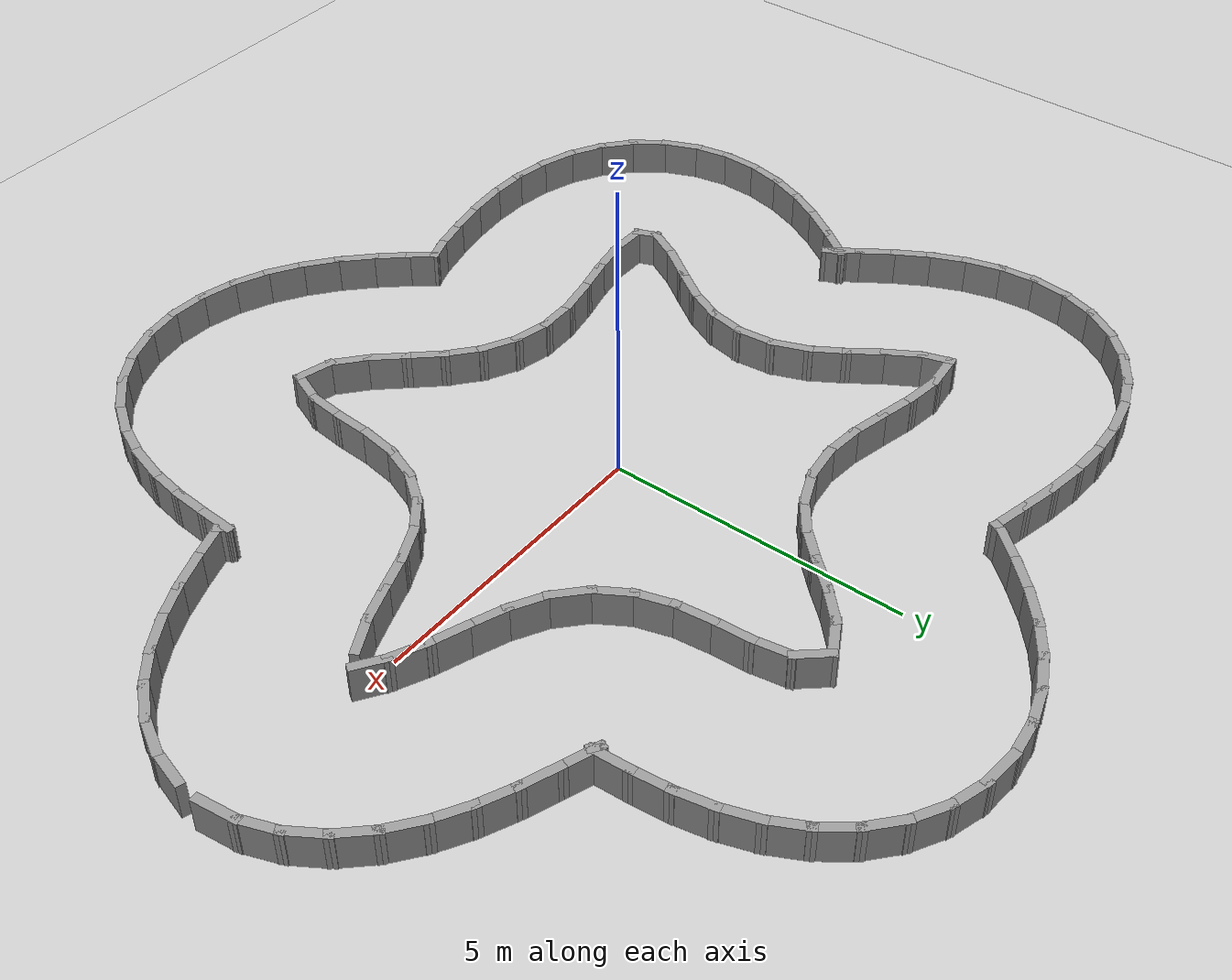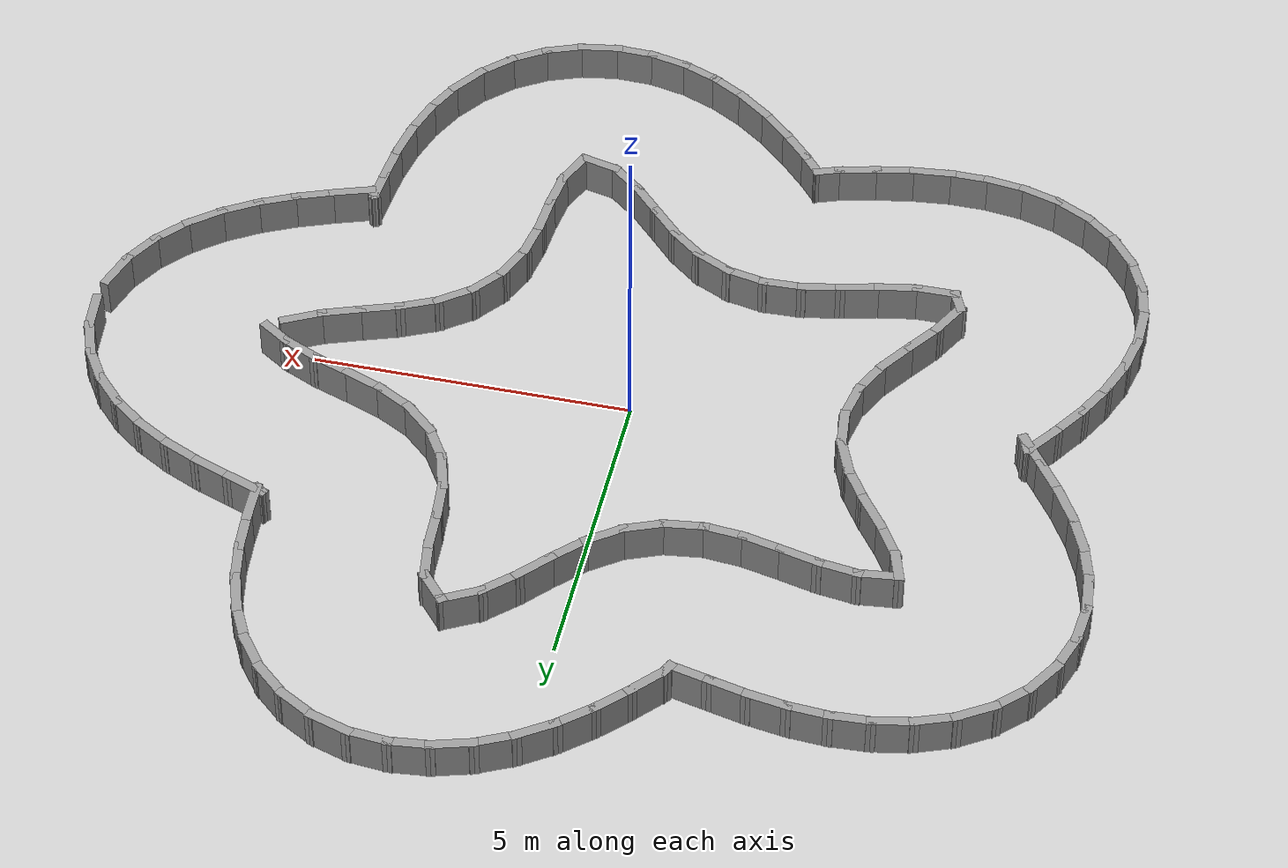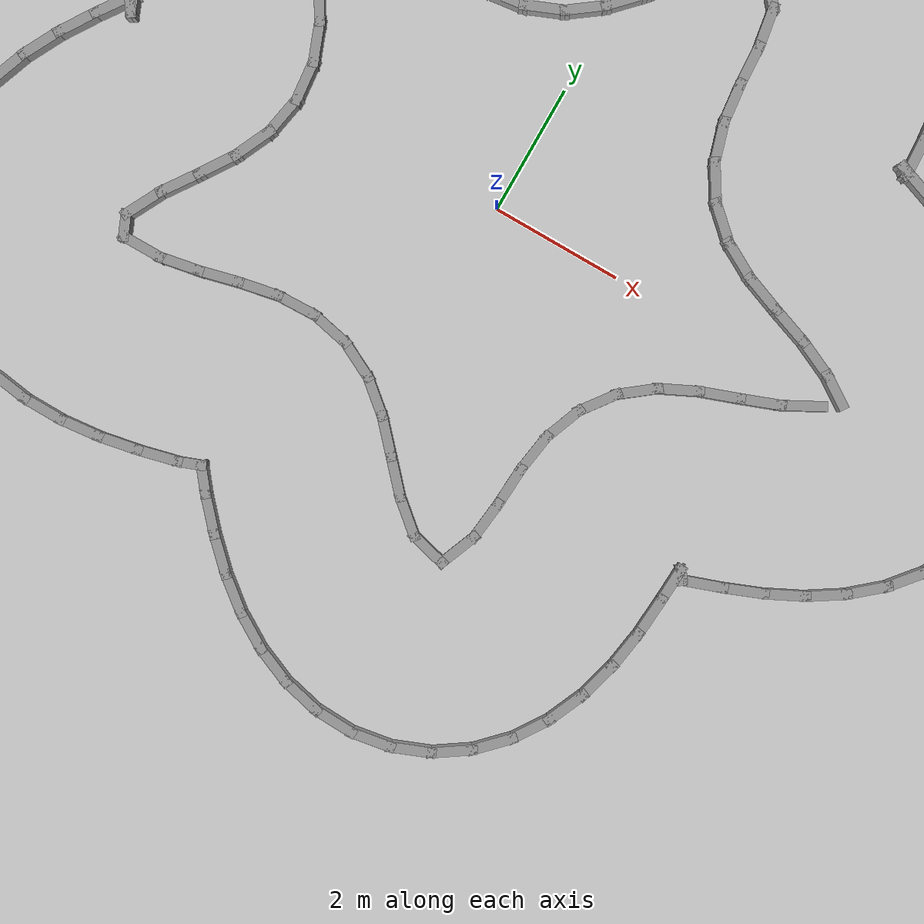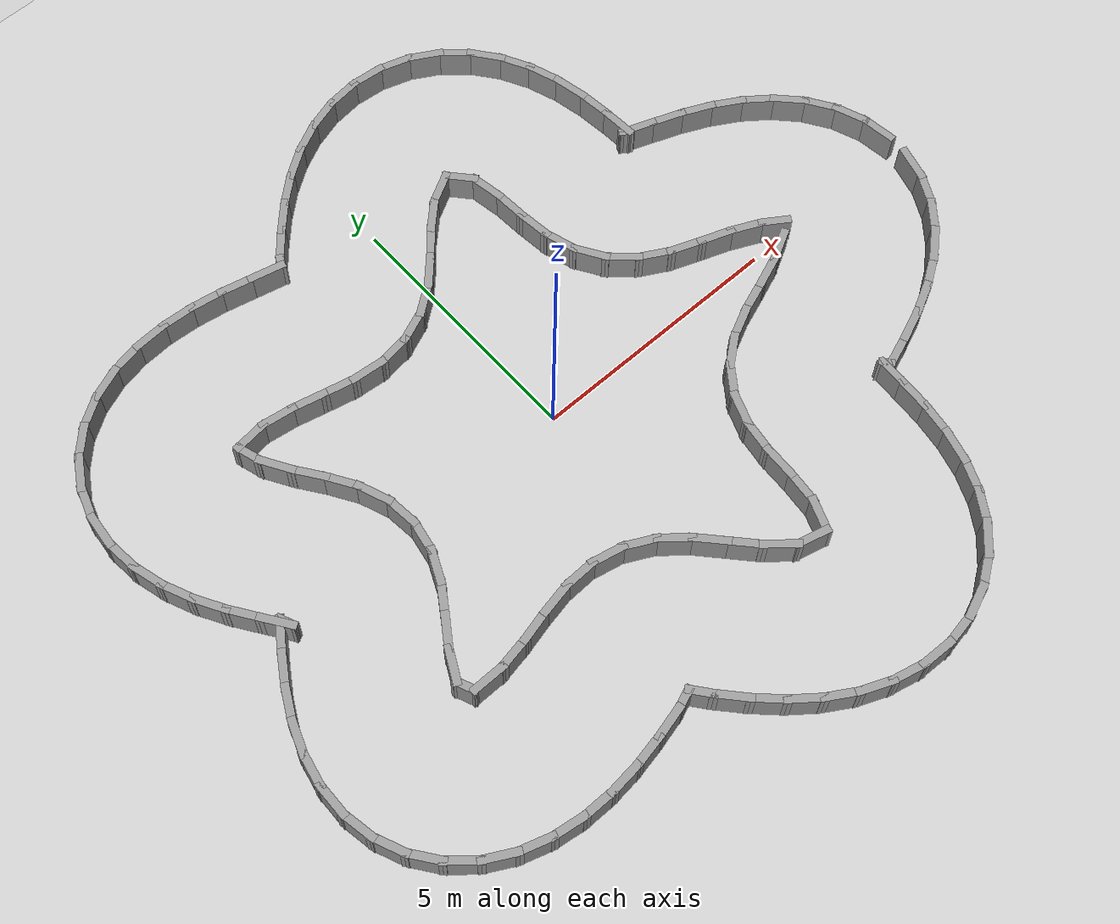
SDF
<?xml version="1.0" ?>
<sdf version='1.7'>
  <world name='default'>
    <plugin name='gazebo_ros_state' filename='libgazebo_ros_state.so'>
      <ros>
        <namespace>/</namespace>
      </ros>
      <update_rate>1000.0</update_rate>
    </plugin>

    <light name='sun' type='directional'>
      <cast_shadows>1</cast_shadows>
      <pose>0 0 10 0 -0 0</pose>
      <diffuse>0.8 0.8 0.8 1</diffuse>
      <specular>0.2 0.2 0.2 1</specular>
      <attenuation>
        <range>1000</range>
        <constant>0.9</constant>
        <linear>0.01</linear>
        <quadratic>0.001</quadratic>
      </attenuation>
      <direction>-0.5 0.1 -0.9</direction>
      <spot>
        <inner_angle>0</inner_angle>
        <outer_angle>0</outer_angle>
        <falloff>0</falloff>
      </spot>
    </light>
    <model name='ground_plane'>
      <static>1</static>
      <link name='link'>
        <collision name='collision'>
          <geometry>
            <plane>
              <normal>0 0 1</normal>
              <size>100 100</size>
            </plane>
          </geometry>
          <surface>
            <friction>
              <ode>
                <mu>100</mu>
                <mu2>50</mu2>
              </ode>
              <torsional>
                <ode/>
              </torsional>
            </friction>
            <contact>
              <ode/>
            </contact>
            <bounce/>
          </surface>
          <max_contacts>10</max_contacts>
        </collision>
        <visual name='visual'>
          <cast_shadows>0</cast_shadows>
          <geometry>
            <plane>
              <normal>0 0 1</normal>
              <size>100 100</size>
            </plane>
          </geometry>
          <material>
            <script>
              <uri>file://media/materials/scripts/gazebo.material</uri>
              <name>Gazebo/Grey</name>
            </script>
          </material>
        </visual>
        <self_collide>0</self_collide>
        <enable_wind>0</enable_wind>
        <kinematic>0</kinematic>
      </link>
    </model>
    <gravity>0 0 -9.8</gravity>
    <magnetic_field>6e-06 2.3e-05 -4.2e-05</magnetic_field>
    <atmosphere type='adiabatic'/>
    <physics type='ode'>
      <max_step_size>0.001</max_step_size>
      <real_time_factor>1</real_time_factor>
      <real_time_update_rate>1000</real_time_update_rate>
    </physics>
    <scene>
      <ambient>0.4 0.4 0.4 1</ambient>
      <background>0.7 0.7 0.7 1</background>
      <shadows>1</shadows>
    </scene>
    <audio>
      <device>default</device>
    </audio>
    <wind/>
    <spherical_coordinates>
      <surface_model>EARTH_WGS84</surface_model>
      <latitude_deg>0</latitude_deg>
      <longitude_deg>0</longitude_deg>
      <elevation>0</elevation>
      <heading_deg>0</heading_deg>
    </spherical_coordinates>
  <model name='rand_lobed_02'>
    <pose>0 0 0 0 -0 0</pose>
    <link name='Wall_0'>
      <collision name='Wall_0_Collision'>
        <geometry><box><size>0.6231 0.1500 0.6000</size></box></geometry>
        <pose>0 0 0.3000 0 -0 0</pose>
      </collision>
      <visual name='Wall_0_Visual'>
        <pose>0 0 0.3000 0 -0 0</pose>
        <geometry><box><size>0.6231 0.1500 0.6000</size></box></geometry>
        <material>
          <script>
            <uri>file://media/materials/scripts/gazebo.material</uri>
            <name>Gazebo/Grey</name>
          </script>
          <ambient>1 1 1 1</ambient>
        </material>
      </visual>
      <pose>5.5545 0.1311 0 0 -0 2.55400</pose>
    </link>
    <link name='Wall_1'>
      <collision name='Wall_1_Collision'>
        <geometry><box><size>0.7494 0.1500 0.6000</size></box></geometry>
        <pose>0 0 0.3000 0 -0 0</pose>
      </collision>
      <visual name='Wall_1_Visual'>
        <pose>0 0 0.3000 0 -0 0</pose>
        <geometry><box><size>0.7494 0.1500 0.6000</size></box></geometry>
        <material>
          <script>
            <uri>file://media/materials/scripts/gazebo.material</uri>
            <name>Gazebo/Grey</name>
          </script>
          <ambient>1 1 1 1</ambient>
        </material>
      </visual>
      <pose>5.0855 0.3879 0 0 -0 2.70903</pose>
    </link>
    <link name='Wall_2'>
      <collision name='Wall_2_Collision'>
        <geometry><box><size>0.7500 0.1500 0.6000</size></box></geometry>
        <pose>0 0 0.3000 0 -0 0</pose>
      </collision>
      <visual name='Wall_2_Visual'>
        <pose>0 0 0.3000 0 -0 0</pose>
        <geometry><box><size>0.7500 0.1500 0.6000</size></box></geometry>
        <material>
          <script>
            <uri>file://media/materials/scripts/gazebo.material</uri>
            <name>Gazebo/Grey</name>
          </script>
          <ambient>1 1 1 1</ambient>
        </material>
      </visual>
      <pose>4.5309 0.6145 0 0 -0 2.79837</pose>
    </link>
    <link name='Wall_3'>
      <collision name='Wall_3_Collision'>
        <geometry><box><size>0.7498 0.1500 0.6000</size></box></geometry>
        <pose>0 0 0.3000 0 -0 0</pose>
      </collision>
      <visual name='Wall_3_Visual'>
        <pose>0 0 0.3000 0 -0 0</pose>
        <geometry><box><size>0.7498 0.1500 0.6000</size></box></geometry>
        <material>
          <script>
            <uri>file://media/materials/scripts/gazebo.material</uri>
            <name>Gazebo/Grey</name>
          </script>
          <ambient>1 1 1 1</ambient>
        </material>
      </visual>
      <pose>3.9682 0.8223 0 0 -0 2.77713</pose>
    </link>
    <link name='Wall_4'>
      <collision name='Wall_4_Collision'>
        <geometry><box><size>0.7490 0.1500 0.6000</size></box></geometry>
        <pose>0 0 0.3000 0 -0 0</pose>
      </collision>
      <visual name='Wall_4_Visual'>
        <pose>0 0 0.3000 0 -0 0</pose>
        <geometry><box><size>0.7490 0.1500 0.6000</size></box></geometry>
        <material>
          <script>
            <uri>file://media/materials/scripts/gazebo.material</uri>
            <name>Gazebo/Grey</name>
          </script>
          <ambient>1 1 1 1</ambient>
        </material>
      </visual>
      <pose>3.4260 1.0744 0 0 -0 2.63553</pose>
    </link>
    <link name='Wall_5'>
      <collision name='Wall_5_Collision'>
        <geometry><box><size>0.7482 0.1500 0.6000</size></box></geometry>
        <pose>0 0 0.3000 0 -0 0</pose>
      </collision>
      <visual name='Wall_5_Visual'>
        <pose>0 0 0.3000 0 -0 0</pose>
        <geometry><box><size>0.7482 0.1500 0.6000</size></box></geometry>
        <material>
          <script>
            <uri>file://media/materials/scripts/gazebo.material</uri>
            <name>Gazebo/Grey</name>
          </script>
          <ambient>1 1 1 1</ambient>
        </material>
      </visual>
      <pose>2.9437 1.4219 0 0 -0 2.39899</pose>
    </link>
    <link name='Wall_6'>
      <collision name='Wall_6_Collision'>
        <geometry><box><size>0.7481 0.1500 0.6000</size></box></geometry>
        <pose>0 0 0.3000 0 -0 0</pose>
      </collision>
      <visual name='Wall_6_Visual'>
        <pose>0 0 0.3000 0 -0 0</pose>
        <geometry><box><size>0.7481 0.1500 0.6000</size></box></geometry>
        <material>
          <script>
            <uri>file://media/materials/scripts/gazebo.material</uri>
            <name>Gazebo/Grey</name>
          </script>
          <ambient>1 1 1 1</ambient>
        </material>
      </visual>
      <pose>2.5665 1.8787 0 0 -0 2.12298</pose>
    </link>
    <link name='Wall_7'>
      <collision name='Wall_7_Collision'>
        <geometry><box><size>0.7486 0.1500 0.6000</size></box></geometry>
        <pose>0 0 0.3000 0 -0 0</pose>
      </collision>
      <visual name='Wall_7_Visual'>
        <pose>0 0 0.3000 0 -0 0</pose>
        <geometry><box><size>0.7486 0.1500 0.6000</size></box></geometry>
        <material>
          <script>
            <uri>file://media/materials/scripts/gazebo.material</uri>
            <name>Gazebo/Grey</name>
          </script>
          <ambient>1 1 1 1</ambient>
        </material>
      </visual>
      <pose>2.3234 2.4199 0 0 -0 1.86292</pose>
    </link>
    <link name='Wall_8'>
      <collision name='Wall_8_Collision'>
        <geometry><box><size>0.7496 0.1500 0.6000</size></box></geometry>
        <pose>0 0 0.3000 0 -0 0</pose>
      </collision>
      <visual name='Wall_8_Visual'>
        <pose>0 0 0.3000 0 -0 0</pose>
        <geometry><box><size>0.7496 0.1500 0.6000</size></box></geometry>
        <material>
          <script>
            <uri>file://media/materials/scripts/gazebo.material</uri>
            <name>Gazebo/Grey</name>
          </script>
          <ambient>1 1 1 1</ambient>
        </material>
      </visual>
      <pose>2.2047 3.0046 0 0 -0 1.67946</pose>
    </link>
    <link name='Wall_9'>
      <collision name='Wall_9_Collision'>
        <geometry><box><size>0.7500 0.1500 0.6000</size></box></geometry>
        <pose>0 0 0.3000 0 -0 0</pose>
      </collision>
      <visual name='Wall_9_Visual'>
        <pose>0 0 0.3000 0 -0 0</pose>
        <geometry><box><size>0.7500 0.1500 0.6000</size></box></geometry>
        <material>
          <script>
            <uri>file://media/materials/scripts/gazebo.material</uri>
            <name>Gazebo/Grey</name>
          </script>
          <ambient>1 1 1 1</ambient>
        </material>
      </visual>
      <pose>2.1546 3.6021 0 0 -0 1.62952</pose>
    </link>
    <link name='Wall_10'>
      <collision name='Wall_10_Collision'>
        <geometry><box><size>0.7491 0.1500 0.6000</size></box></geometry>
        <pose>0 0 0.3000 0 -0 0</pose>
      </collision>
      <visual name='Wall_10_Visual'>
        <pose>0 0 0.3000 0 -0 0</pose>
        <geometry><box><size>0.7491 0.1500 0.6000</size></box></geometry>
        <material>
          <script>
            <uri>file://media/materials/scripts/gazebo.material</uri>
            <name>Gazebo/Grey</name>
          </script>
          <ambient>1 1 1 1</ambient>
        </material>
      </visual>
      <pose>2.0881 4.1971 0 0 -0 1.73457</pose>
    </link>
    <link name='Wall_11'>
      <collision name='Wall_11_Collision'>
        <geometry><box><size>0.6831 0.1500 0.6000</size></box></geometry>
        <pose>0 0 0.3000 0 -0 0</pose>
      </collision>
      <visual name='Wall_11_Visual'>
        <pose>0 0 0.3000 0 -0 0</pose>
        <geometry><box><size>0.6831 0.1500 0.6000</size></box></geometry>
        <material>
          <script>
            <uri>file://media/materials/scripts/gazebo.material</uri>
            <name>Gazebo/Grey</name>
          </script>
          <ambient>1 1 1 1</ambient>
        </material>
      </visual>
      <pose>1.8645 4.6938 0 0 -0 2.28624</pose>
    </link>
    <link name='Wall_12'>
      <collision name='Wall_12_Collision'>
        <geometry><box><size>0.7454 0.1500 0.6000</size></box></geometry>
        <pose>0 0 0.3000 0 -0 0</pose>
      </collision>
      <visual name='Wall_12_Visual'>
        <pose>0 0 0.3000 0 -0 0</pose>
        <geometry><box><size>0.7454 0.1500 0.6000</size></box></geometry>
        <material>
          <script>
            <uri>file://media/materials/scripts/gazebo.material</uri>
            <name>Gazebo/Grey</name>
          </script>
          <ambient>1 1 1 1</ambient>
        </material>
      </visual>
      <pose>1.4286 4.7518 0 0 -0 -2.63997</pose>
    </link>
    <link name='Wall_13'>
      <collision name='Wall_13_Collision'>
        <geometry><box><size>0.7494 0.1500 0.6000</size></box></geometry>
        <pose>0 0 0.3000 0 -0 0</pose>
      </collision>
      <visual name='Wall_13_Visual'>
        <pose>0 0 0.3000 0 -0 0</pose>
        <geometry><box><size>0.7494 0.1500 0.6000</size></box></geometry>
        <material>
          <script>
            <uri>file://media/materials/scripts/gazebo.material</uri>
            <name>Gazebo/Grey</name>
          </script>
          <ambient>1 1 1 1</ambient>
        </material>
      </visual>
      <pose>0.9505 4.4020 0 0 -0 -2.38054</pose>
    </link>
    <link name='Wall_14'>
      <collision name='Wall_14_Collision'>
        <geometry><box><size>0.7500 0.1500 0.6000</size></box></geometry>
        <pose>0 0 0.3000 0 -0 0</pose>
      </collision>
      <visual name='Wall_14_Visual'>
        <pose>0 0 0.3000 0 -0 0</pose>
        <geometry><box><size>0.7500 0.1500 0.6000</size></box></geometry>
        <material>
          <script>
            <uri>file://media/materials/scripts/gazebo.material</uri>
            <name>Gazebo/Grey</name>
          </script>
          <ambient>1 1 1 1</ambient>
        </material>
      </visual>
      <pose>0.5348 3.9705 0 0 -0 -2.29493</pose>
    </link>
    <link name='Wall_15'>
      <collision name='Wall_15_Collision'>
        <geometry><box><size>0.7497 0.1500 0.6000</size></box></geometry>
        <pose>0 0 0.3000 0 -0 0</pose>
      </collision>
      <visual name='Wall_15_Visual'>
        <pose>0 0 0.3000 0 -0 0</pose>
        <geometry><box><size>0.7497 0.1500 0.6000</size></box></geometry>
        <material>
          <script>
            <uri>file://media/materials/scripts/gazebo.material</uri>
            <name>Gazebo/Grey</name>
          </script>
          <ambient>1 1 1 1</ambient>
        </material>
      </visual>
      <pose>0.1277 3.5302 0 0 -0 -2.33905</pose>
    </link>
    <link name='Wall_16'>
      <collision name='Wall_16_Collision'>
        <geometry><box><size>0.7488 0.1500 0.6000</size></box></geometry>
        <pose>0 0 0.3000 0 -0 0</pose>
      </collision>
      <visual name='Wall_16_Visual'>
        <pose>0 0 0.3000 0 -0 0</pose>
        <geometry><box><size>0.7488 0.1500 0.6000</size></box></geometry>
        <material>
          <script>
            <uri>file://media/materials/scripts/gazebo.material</uri>
            <name>Gazebo/Grey</name>
          </script>
          <ambient>1 1 1 1</ambient>
        </material>
      </visual>
      <pose>-0.3218 3.1370 0 0 -0 -2.50682</pose>
    </link>
    <link name='Wall_17'>
      <collision name='Wall_17_Collision'>
        <geometry><box><size>0.7483 0.1500 0.6000</size></box></geometry>
        <pose>0 0 0.3000 0 -0 0</pose>
      </collision>
      <visual name='Wall_17_Visual'>
        <pose>0 0 0.3000 0 -0 0</pose>
        <geometry><box><size>0.7483 0.1500 0.6000</size></box></geometry>
        <material>
          <script>
            <uri>file://media/materials/scripts/gazebo.material</uri>
            <name>Gazebo/Grey</name>
          </script>
          <ambient>1 1 1 1</ambient>
        </material>
      </visual>
      <pose>-0.8395 2.8456 0 0 -0 -2.75114</pose>
    </link>
    <link name='Wall_18'>
      <collision name='Wall_18_Collision'>
        <geometry><box><size>0.7484 0.1500 0.6000</size></box></geometry>
        <pose>0 0 0.3000 0 -0 0</pose>
      </collision>
      <visual name='Wall_18_Visual'>
        <pose>0 0 0.3000 0 -0 0</pose>
        <geometry><box><size>0.7484 0.1500 0.6000</size></box></geometry>
        <material>
          <script>
            <uri>file://media/materials/scripts/gazebo.material</uri>
            <name>Gazebo/Grey</name>
          </script>
          <ambient>1 1 1 1</ambient>
        </material>
      </visual>
      <pose>-1.4128 2.6932 0 0 -0 -3.01212</pose>
    </link>
    <link name='Wall_19'>
      <collision name='Wall_19_Collision'>
        <geometry><box><size>0.7491 0.1500 0.6000</size></box></geometry>
        <pose>0 0 0.3000 0 -0 0</pose>
      </collision>
      <visual name='Wall_19_Visual'>
        <pose>0 0 0.3000 0 -0 0</pose>
        <geometry><box><size>0.7491 0.1500 0.6000</size></box></geometry>
        <material>
          <script>
            <uri>file://media/materials/scripts/gazebo.material</uri>
            <name>Gazebo/Grey</name>
          </script>
          <ambient>1 1 1 1</ambient>
        </material>
      </visual>
      <pose>-2.0077 2.6823 0 0 -0 3.04875</pose>
    </link>
    <link name='Wall_20'>
      <collision name='Wall_20_Collision'>
        <geometry><box><size>0.7499 0.1500 0.6000</size></box></geometry>
        <pose>0 0 0.3000 0 -0 0</pose>
      </collision>
      <visual name='Wall_20_Visual'>
        <pose>0 0 0.3000 0 -0 0</pose>
        <geometry><box><size>0.7499 0.1500 0.6000</size></box></geometry>
        <material>
          <script>
            <uri>file://media/materials/scripts/gazebo.material</uri>
            <name>Gazebo/Grey</name>
          </script>
          <ambient>1 1 1 1</ambient>
        </material>
      </visual>
      <pose>-2.5986 2.7760 0 0 -0 2.92006</pose>
    </link>
    <link name='Wall_21'>
      <collision name='Wall_21_Collision'>
        <geometry><box><size>0.7500 0.1500 0.6000</size></box></geometry>
        <pose>0 0 0.3000 0 -0 0</pose>
      </collision>
      <visual name='Wall_21_Visual'>
        <pose>0 0 0.3000 0 -0 0</pose>
        <geometry><box><size>0.7500 0.1500 0.6000</size></box></geometry>
        <material>
          <script>
            <uri>file://media/materials/scripts/gazebo.material</uri>
            <name>Gazebo/Grey</name>
          </script>
          <ambient>1 1 1 1</ambient>
        </material>
      </visual>
      <pose>-3.1830 2.9114 0 0 -0 2.90779</pose>
    </link>
    <link name='Wall_22'>
      <collision name='Wall_22_Collision'>
        <geometry><box><size>0.7495 0.1500 0.6000</size></box></geometry>
        <pose>0 0 0.3000 0 -0 0</pose>
      </collision>
      <visual name='Wall_22_Visual'>
        <pose>0 0 0.3000 0 -0 0</pose>
        <geometry><box><size>0.7495 0.1500 0.6000</size></box></geometry>
        <material>
          <script>
            <uri>file://media/materials/scripts/gazebo.material</uri>
            <name>Gazebo/Grey</name>
          </script>
          <ambient>1 1 1 1</ambient>
        </material>
      </visual>
      <pose>-3.7716 3.0230 0 0 -0 3.00070</pose>
    </link>
    <link name='Wall_23'>
      <collision name='Wall_23_Collision'>
        <geometry><box><size>0.7453 0.1500 0.6000</size></box></geometry>
        <pose>0 0 0.3000 0 -0 0</pose>
      </collision>
      <visual name='Wall_23_Visual'>
        <pose>0 0 0.3000 0 -0 0</pose>
        <geometry><box><size>0.7453 0.1500 0.6000</size></box></geometry>
        <material>
          <script>
            <uri>file://media/materials/scripts/gazebo.material</uri>
            <name>Gazebo/Grey</name>
          </script>
          <ambient>1 1 1 1</ambient>
        </material>
      </visual>
      <pose>-4.3642 3.0321 0 0 -0 -3.03064</pose>
    </link>
    <link name='Wall_24'>
      <collision name='Wall_24_Collision'>
        <geometry><box><size>0.5952 0.1500 0.6000</size></box></geometry>
        <pose>0 0 0.3000 0 -0 0</pose>
      </collision>
      <visual name='Wall_24_Visual'>
        <pose>0 0 0.3000 0 -0 0</pose>
        <geometry><box><size>0.5952 0.1500 0.6000</size></box></geometry>
        <material>
          <script>
            <uri>file://media/materials/scripts/gazebo.material</uri>
            <name>Gazebo/Grey</name>
          </script>
          <ambient>1 1 1 1</ambient>
        </material>
      </visual>
      <pose>-4.5961 2.7860 0 0 -0 -1.27937</pose>
    </link>
    <link name='Wall_25'>
      <collision name='Wall_25_Collision'>
        <geometry><box><size>0.7494 0.1500 0.6000</size></box></geometry>
        <pose>0 0 0.3000 0 -0 0</pose>
      </collision>
      <visual name='Wall_25_Visual'>
        <pose>0 0 0.3000 0 -0 0</pose>
        <geometry><box><size>0.7494 0.1500 0.6000</size></box></geometry>
        <material>
          <script>
            <uri>file://media/materials/scripts/gazebo.material</uri>
            <name>Gazebo/Grey</name>
          </script>
          <ambient>1 1 1 1</ambient>
        </material>
      </visual>
      <pose>-4.3782 2.3156 0 0 -0 -1.03138</pose>
    </link>
    <link name='Wall_26'>
      <collision name='Wall_26_Collision'>
        <geometry><box><size>0.7500 0.1500 0.6000</size></box></geometry>
        <pose>0 0 0.3000 0 -0 0</pose>
      </collision>
      <visual name='Wall_26_Visual'>
        <pose>0 0 0.3000 0 -0 0</pose>
        <geometry><box><size>0.7500 0.1500 0.6000</size></box></geometry>
        <material>
          <script>
            <uri>file://media/materials/scripts/gazebo.material</uri>
            <name>Gazebo/Grey</name>
          </script>
          <ambient>1 1 1 1</ambient>
        </material>
      </visual>
      <pose>-4.0508 1.8137 0 0 -0 -0.95438</pose>
    </link>
    <link name='Wall_27'>
      <collision name='Wall_27_Collision'>
        <geometry><box><size>0.7496 0.1500 0.6000</size></box></geometry>
        <pose>0 0 0.3000 0 -0 0</pose>
      </collision>
      <visual name='Wall_27_Visual'>
        <pose>0 0 0.3000 0 -0 0</pose>
        <geometry><box><size>0.7496 0.1500 0.6000</size></box></geometry>
        <material>
          <script>
            <uri>file://media/materials/scripts/gazebo.material</uri>
            <name>Gazebo/Grey</name>
          </script>
          <ambient>1 1 1 1</ambient>
        </material>
      </visual>
      <pose>-3.7194 1.3141 0 0 -0 -1.01584</pose>
    </link>
    <link name='Wall_28'>
      <collision name='Wall_28_Collision'>
        <geometry><box><size>0.7486 0.1500 0.6000</size></box></geometry>
        <pose>0 0 0.3000 0 -0 0</pose>
      </collision>
      <visual name='Wall_28_Visual'>
        <pose>0 0 0.3000 0 -0 0</pose>
        <geometry><box><size>0.7486 0.1500 0.6000</size></box></geometry>
        <material>
          <script>
            <uri>file://media/materials/scripts/gazebo.material</uri>
            <name>Gazebo/Grey</name>
          </script>
          <ambient>1 1 1 1</ambient>
        </material>
      </visual>
      <pose>-3.4545 0.7798 0 0 -0 -1.20536</pose>
    </link>
    <link name='Wall_29'>
      <collision name='Wall_29_Collision'>
        <geometry><box><size>0.7479 0.1500 0.6000</size></box></geometry>
        <pose>0 0 0.3000 0 -0 0</pose>
      </collision>
      <visual name='Wall_29_Visual'>
        <pose>0 0 0.3000 0 -0 0</pose>
        <geometry><box><size>0.7479 0.1500 0.6000</size></box></geometry>
        <material>
          <script>
            <uri>file://media/materials/scripts/gazebo.material</uri>
            <name>Gazebo/Grey</name>
          </script>
          <ambient>1 1 1 1</ambient>
        </material>
      </visual>
      <pose>-3.3183 0.2027 0 0 -0 -1.47272</pose>
    </link>
    <link name='Wall_30'>
      <collision name='Wall_30_Collision'>
        <geometry><box><size>0.7480 0.1500 0.6000</size></box></geometry>
        <pose>0 0 0.3000 0 -0 0</pose>
      </collision>
      <visual name='Wall_30_Visual'>
        <pose>0 0 0.3000 0 -0 0</pose>
        <geometry><box><size>0.7480 0.1500 0.6000</size></box></geometry>
        <material>
          <script>
            <uri>file://media/materials/scripts/gazebo.material</uri>
            <name>Gazebo/Grey</name>
          </script>
          <ambient>1 1 1 1</ambient>
        </material>
      </visual>
      <pose>-3.3446 -0.3886 0 0 -0 -1.75793</pose>
    </link>
    <link name='Wall_31'>
      <collision name='Wall_31_Collision'>
        <geometry><box><size>0.7489 0.1500 0.6000</size></box></geometry>
        <pose>0 0 0.3000 0 -0 0</pose>
      </collision>
      <visual name='Wall_31_Visual'>
        <pose>0 0 0.3000 0 -0 0</pose>
        <geometry><box><size>0.7489 0.1500 0.6000</size></box></geometry>
        <material>
          <script>
            <uri>file://media/materials/scripts/gazebo.material</uri>
            <name>Gazebo/Grey</name>
          </script>
          <ambient>1 1 1 1</ambient>
        </material>
      </visual>
      <pose>-3.5269 -0.9537 0 0 -0 -2.00754</pose>
    </link>
    <link name='Wall_32'>
      <collision name='Wall_32_Collision'>
        <geometry><box><size>0.7498 0.1500 0.6000</size></box></geometry>
        <pose>0 0 0.3000 0 -0 0</pose>
      </collision>
      <visual name='Wall_32_Visual'>
        <pose>0 0 0.3000 0 -0 0</pose>
        <geometry><box><size>0.7498 0.1500 0.6000</size></box></geometry>
        <material>
          <script>
            <uri>file://media/materials/scripts/gazebo.material</uri>
            <name>Gazebo/Grey</name>
          </script>
          <ambient>1 1 1 1</ambient>
        </material>
      </visual>
      <pose>-3.8203 -1.4743 0 0 -0 -2.16019</pose>
    </link>
    <link name='Wall_33'>
      <collision name='Wall_33_Collision'>
        <geometry><box><size>0.7499 0.1500 0.6000</size></box></geometry>
        <pose>0 0 0.3000 0 -0 0</pose>
      </collision>
      <visual name='Wall_33_Visual'>
        <pose>0 0 0.3000 0 -0 0</pose>
        <geometry><box><size>0.7499 0.1500 0.6000</size></box></geometry>
        <material>
          <script>
            <uri>file://media/materials/scripts/gazebo.material</uri>
            <name>Gazebo/Grey</name>
          </script>
          <ambient>1 1 1 1</ambient>
        </material>
      </visual>
      <pose>-4.1581 -1.9700 0 0 -0 -2.17801</pose>
    </link>
    <link name='Wall_34'>
      <collision name='Wall_34_Collision'>
        <geometry><box><size>0.7488 0.1500 0.6000</size></box></geometry>
        <pose>0 0 0.3000 0 -0 0</pose>
      </collision>
      <visual name='Wall_34_Visual'>
        <pose>0 0 0.3000 0 -0 0</pose>
        <geometry><box><size>0.7488 0.1500 0.6000</size></box></geometry>
        <material>
          <script>
            <uri>file://media/materials/scripts/gazebo.material</uri>
            <name>Gazebo/Grey</name>
          </script>
          <ambient>1 1 1 1</ambient>
        </material>
      </visual>
      <pose>-4.4678 -2.4818 0 0 -0 -2.05165</pose>
    </link>
    <link name='Wall_35'>
      <collision name='Wall_35_Collision'>
        <geometry><box><size>0.4783 0.1500 0.6000</size></box></geometry>
        <pose>0 0 0.3000 0 -0 0</pose>
      </collision>
      <visual name='Wall_35_Visual'>
        <pose>0 0 0.3000 0 -0 0</pose>
        <geometry><box><size>0.4783 0.1500 0.6000</size></box></geometry>
        <material>
          <script>
            <uri>file://media/materials/scripts/gazebo.material</uri>
            <name>Gazebo/Grey</name>
          </script>
          <ambient>1 1 1 1</ambient>
        </material>
      </visual>
      <pose>-4.5419 -2.8983 0 0 -0 -1.16822</pose>
    </link>
    <link name='Wall_36'>
      <collision name='Wall_36_Collision'>
        <geometry><box><size>0.7481 0.1500 0.6000</size></box></geometry>
        <pose>0 0 0.3000 0 -0 0</pose>
      </collision>
      <visual name='Wall_36_Visual'>
        <pose>0 0 0.3000 0 -0 0</pose>
        <geometry><box><size>0.7481 0.1500 0.6000</size></box></geometry>
        <material>
          <script>
            <uri>file://media/materials/scripts/gazebo.material</uri>
            <name>Gazebo/Grey</name>
          </script>
          <ambient>1 1 1 1</ambient>
        </material>
      </visual>
      <pose>-4.1786 -3.0488 0 0 -0 0.00166</pose>
    </link>
    <link name='Wall_37'>
      <collision name='Wall_37_Collision'>
        <geometry><box><size>0.7497 0.1500 0.6000</size></box></geometry>
        <pose>0 0 0.3000 0 -0 0</pose>
      </collision>
      <visual name='Wall_37_Visual'>
        <pose>0 0 0.3000 0 -0 0</pose>
        <geometry><box><size>0.7497 0.1500 0.6000</size></box></geometry>
        <material>
          <script>
            <uri>file://media/materials/scripts/gazebo.material</uri>
            <name>Gazebo/Grey</name>
          </script>
          <ambient>1 1 1 1</ambient>
        </material>
      </visual>
      <pose>-3.5846 -2.9942 0 0 -0 0.18162</pose>
    </link>
    <link name='Wall_38'>
      <collision name='Wall_38_Collision'>
        <geometry><box><size>0.7500 0.1500 0.6000</size></box></geometry>
        <pose>0 0 0.3000 0 -0 0</pose>
      </collision>
      <visual name='Wall_38_Visual'>
        <pose>0 0 0.3000 0 -0 0</pose>
        <geometry><box><size>0.7500 0.1500 0.6000</size></box></geometry>
        <material>
          <script>
            <uri>file://media/materials/scripts/gazebo.material</uri>
            <name>Gazebo/Grey</name>
          </script>
          <ambient>1 1 1 1</ambient>
        </material>
      </visual>
      <pose>-2.9984 -2.8681 0 0 -0 0.24187</pose>
    </link>
    <link name='Wall_39'>
      <collision name='Wall_39_Collision'>
        <geometry><box><size>0.7497 0.1500 0.6000</size></box></geometry>
        <pose>0 0 0.3000 0 -0 0</pose>
      </collision>
      <visual name='Wall_39_Visual'>
        <pose>0 0 0.3000 0 -0 0</pose>
        <geometry><box><size>0.7497 0.1500 0.6000</size></box></geometry>
        <material>
          <script>
            <uri>file://media/materials/scripts/gazebo.material</uri>
            <name>Gazebo/Grey</name>
          </script>
          <ambient>1 1 1 1</ambient>
        </material>
      </visual>
      <pose>-2.4129 -2.7387 0 0 -0 0.19341</pose>
    </link>
    <link name='Wall_40'>
      <collision name='Wall_40_Collision'>
        <geometry><box><size>0.7489 0.1500 0.6000</size></box></geometry>
        <pose>0 0 0.3000 0 -0 0</pose>
      </collision>
      <visual name='Wall_40_Visual'>
        <pose>0 0 0.3000 0 -0 0</pose>
        <geometry><box><size>0.7489 0.1500 0.6000</size></box></geometry>
        <material>
          <script>
            <uri>file://media/materials/scripts/gazebo.material</uri>
            <name>Gazebo/Grey</name>
          </script>
          <ambient>1 1 1 1</ambient>
        </material>
      </visual>
      <pose>-1.8193 -2.6720 0 0 -0 0.03029</pose>
    </link>
    <link name='Wall_41'>
      <collision name='Wall_41_Collision'>
        <geometry><box><size>0.7483 0.1500 0.6000</size></box></geometry>
        <pose>0 0 0.3000 0 -0 0</pose>
      </collision>
      <visual name='Wall_41_Visual'>
        <pose>0 0 0.3000 0 -0 0</pose>
        <geometry><box><size>0.7483 0.1500 0.6000</size></box></geometry>
        <material>
          <script>
            <uri>file://media/materials/scripts/gazebo.material</uri>
            <name>Gazebo/Grey</name>
          </script>
          <ambient>1 1 1 1</ambient>
        </material>
      </visual>
      <pose>-1.2275 -2.7254 0 0 -0 -0.21041</pose>
    </link>
    <link name='Wall_42'>
      <collision name='Wall_42_Collision'>
        <geometry><box><size>0.7484 0.1500 0.6000</size></box></geometry>
        <pose>0 0 0.3000 0 -0 0</pose>
      </collision>
      <visual name='Wall_42_Visual'>
        <pose>0 0 0.3000 0 -0 0</pose>
        <geometry><box><size>0.7484 0.1500 0.6000</size></box></geometry>
        <material>
          <script>
            <uri>file://media/materials/scripts/gazebo.material</uri>
            <name>Gazebo/Grey</name>
          </script>
          <ambient>1 1 1 1</ambient>
        </material>
      </visual>
      <pose>-0.6685 -2.9239 0 0 -0 -0.47214</pose>
    </link>
    <link name='Wall_43'>
      <collision name='Wall_43_Collision'>
        <geometry><box><size>0.7491 0.1500 0.6000</size></box></geometry>
        <pose>0 0 0.3000 0 -0 0</pose>
      </collision>
      <visual name='Wall_43_Visual'>
        <pose>0 0 0.3000 0 -0 0</pose>
        <geometry><box><size>0.7491 0.1500 0.6000</size></box></geometry>
        <material>
          <script>
            <uri>file://media/materials/scripts/gazebo.material</uri>
            <name>Gazebo/Grey</name>
          </script>
          <ambient>1 1 1 1</ambient>
        </material>
      </visual>
      <pose>-0.1728 -3.2527 0 0 -0 -0.69901</pose>
    </link>
    <link name='Wall_44'>
      <collision name='Wall_44_Collision'>
        <geometry><box><size>0.7499 0.1500 0.6000</size></box></geometry>
        <pose>0 0 0.3000 0 -0 0</pose>
      </collision>
      <visual name='Wall_44_Visual'>
        <pose>0 0 0.3000 0 -0 0</pose>
        <geometry><box><size>0.7499 0.1500 0.6000</size></box></geometry>
        <material>
          <script>
            <uri>file://media/materials/scripts/gazebo.material</uri>
            <name>Gazebo/Grey</name>
          </script>
          <ambient>1 1 1 1</ambient>
        </material>
      </visual>
      <pose>0.2588 -3.6670 0 0 -0 -0.83092</pose>
    </link>
    <link name='Wall_45'>
      <collision name='Wall_45_Collision'>
        <geometry><box><size>0.7499 0.1500 0.6000</size></box></geometry>
        <pose>0 0 0.3000 0 -0 0</pose>
      </collision>
      <visual name='Wall_45_Visual'>
        <pose>0 0 0.3000 0 -0 0</pose>
        <geometry><box><size>0.7499 0.1500 0.6000</size></box></geometry>
        <material>
          <script>
            <uri>file://media/materials/scripts/gazebo.material</uri>
            <name>Gazebo/Grey</name>
          </script>
          <ambient>1 1 1 1</ambient>
        </material>
      </visual>
      <pose>0.6627 -4.1105 0 0 -0 -0.83336</pose>
    </link>
    <link name='Wall_46'>
      <collision name='Wall_46_Collision'>
        <geometry><box><size>0.7490 0.1500 0.6000</size></box></geometry>
        <pose>0 0 0.3000 0 -0 0</pose>
      </collision>
      <visual name='Wall_46_Visual'>
        <pose>0 0 0.3000 0 -0 0</pose>
        <geometry><box><size>0.7490 0.1500 0.6000</size></box></geometry>
        <material>
          <script>
            <uri>file://media/materials/scripts/gazebo.material</uri>
            <name>Gazebo/Grey</name>
          </script>
          <ambient>1 1 1 1</ambient>
        </material>
      </visual>
      <pose>1.0924 -4.5267 0 0 -0 -0.70524</pose>
    </link>
    <link name='Wall_47'>
      <collision name='Wall_47_Collision'>
        <geometry><box><size>0.7100 0.1500 0.6000</size></box></geometry>
        <pose>0 0 0.3000 0 -0 0</pose>
      </collision>
      <visual name='Wall_47_Visual'>
        <pose>0 0 0.3000 0 -0 0</pose>
        <geometry><box><size>0.7100 0.1500 0.6000</size></box></geometry>
        <material>
          <script>
            <uri>file://media/materials/scripts/gazebo.material</uri>
            <name>Gazebo/Grey</name>
          </script>
          <ambient>1 1 1 1</ambient>
        </material>
      </visual>
      <pose>1.5917 -4.7902 0 0 -0 -0.25059</pose>
    </link>
    <link name='Wall_48'>
      <collision name='Wall_48_Collision'>
        <geometry><box><size>0.7439 0.1500 0.6000</size></box></geometry>
        <pose>0 0 0.3000 0 -0 0</pose>
      </collision>
      <visual name='Wall_48_Visual'>
        <pose>0 0 0.3000 0 -0 0</pose>
        <geometry><box><size>0.7439 0.1500 0.6000</size></box></geometry>
        <material>
          <script>
            <uri>file://media/materials/scripts/gazebo.material</uri>
            <name>Gazebo/Grey</name>
          </script>
          <ambient>1 1 1 1</ambient>
        </material>
      </visual>
      <pose>1.9731 -4.5839 0 0 -0 1.19066</pose>
    </link>
    <link name='Wall_49'>
      <collision name='Wall_49_Collision'>
        <geometry><box><size>0.7496 0.1500 0.6000</size></box></geometry>
        <pose>0 0 0.3000 0 -0 0</pose>
      </collision>
      <visual name='Wall_49_Visual'>
        <pose>0 0 0.3000 0 -0 0</pose>
        <geometry><box><size>0.7496 0.1500 0.6000</size></box></geometry>
        <material>
          <script>
            <uri>file://media/materials/scripts/gazebo.material</uri>
            <name>Gazebo/Grey</name>
          </script>
          <ambient>1 1 1 1</ambient>
        </material>
      </visual>
      <pose>2.1168 -4.0103 0 0 -0 1.45869</pose>
    </link>
    <link name='Wall_50'>
      <collision name='Wall_50_Collision'>
        <geometry><box><size>0.7500 0.1500 0.6000</size></box></geometry>
        <pose>0 0 0.3000 0 -0 0</pose>
      </collision>
      <visual name='Wall_50_Visual'>
        <pose>0 0 0.3000 0 -0 0</pose>
        <geometry><box><size>0.7500 0.1500 0.6000</size></box></geometry>
        <material>
          <script>
            <uri>file://media/materials/scripts/gazebo.material</uri>
            <name>Gazebo/Grey</name>
          </script>
          <ambient>1 1 1 1</ambient>
        </material>
      </visual>
      <pose>2.1678 -3.4129 0 0 -0 1.51250</pose>
    </link>
    <link name='Wall_51'>
      <collision name='Wall_51_Collision'>
        <geometry><box><size>0.7493 0.1500 0.6000</size></box></geometry>
        <pose>0 0 0.3000 0 -0 0</pose>
      </collision>
      <visual name='Wall_51_Visual'>
        <pose>0 0 0.3000 0 -0 0</pose>
        <geometry><box><size>0.7493 0.1500 0.6000</size></box></geometry>
        <material>
          <script>
            <uri>file://media/materials/scripts/gazebo.material</uri>
            <name>Gazebo/Grey</name>
          </script>
          <ambient>1 1 1 1</ambient>
        </material>
      </visual>
      <pose>2.2314 -2.8173 0 0 -0 1.41642</pose>
    </link>
    <link name='Wall_52'>
      <collision name='Wall_52_Collision'>
        <geometry><box><size>0.7484 0.1500 0.6000</size></box></geometry>
        <pose>0 0 0.3000 0 -0 0</pose>
      </collision>
      <visual name='Wall_52_Visual'>
        <pose>0 0 0.3000 0 -0 0</pose>
        <geometry><box><size>0.7484 0.1500 0.6000</size></box></geometry>
        <material>
          <script>
            <uri>file://media/materials/scripts/gazebo.material</uri>
            <name>Gazebo/Grey</name>
          </script>
          <ambient>1 1 1 1</ambient>
        </material>
      </visual>
      <pose>2.3854 -2.2422 0 0 -0 1.20157</pose>
    </link>
    <link name='Wall_53'>
      <collision name='Wall_53_Collision'>
        <geometry><box><size>0.7480 0.1500 0.6000</size></box></geometry>
        <pose>0 0 0.3000 0 -0 0</pose>
      </collision>
      <visual name='Wall_53_Visual'>
        <pose>0 0 0.3000 0 -0 0</pose>
        <geometry><box><size>0.7480 0.1500 0.6000</size></box></geometry>
        <material>
          <script>
            <uri>file://media/materials/scripts/gazebo.material</uri>
            <name>Gazebo/Grey</name>
          </script>
          <ambient>1 1 1 1</ambient>
        </material>
      </visual>
      <pose>2.6720 -1.7234 0 0 -0 0.93051</pose>
    </link>
    <link name='Wall_54'>
      <collision name='Wall_54_Collision'>
        <geometry><box><size>0.7484 0.1500 0.6000</size></box></geometry>
        <pose>0 0 0.3000 0 -0 0</pose>
      </collision>
      <visual name='Wall_54_Visual'>
        <pose>0 0 0.3000 0 -0 0</pose>
        <geometry><box><size>0.7484 0.1500 0.6000</size></box></geometry>
        <material>
          <script>
            <uri>file://media/materials/scripts/gazebo.material</uri>
            <name>Gazebo/Grey</name>
          </script>
          <ambient>1 1 1 1</ambient>
        </material>
      </visual>
      <pose>3.0868 -1.3000 0 0 -0 0.66095</pose>
    </link>
    <link name='Wall_55'>
      <collision name='Wall_55_Collision'>
        <geometry><box><size>0.7493 0.1500 0.6000</size></box></geometry>
        <pose>0 0 0.3000 0 -0 0</pose>
      </collision>
      <visual name='Wall_55_Visual'>
        <pose>0 0 0.3000 0 -0 0</pose>
        <geometry><box><size>0.7493 0.1500 0.6000</size></box></geometry>
        <material>
          <script>
            <uri>file://media/materials/scripts/gazebo.material</uri>
            <name>Gazebo/Grey</name>
          </script>
          <ambient>1 1 1 1</ambient>
        </material>
      </visual>
      <pose>3.5930 -0.9863 0 0 -0 0.44876</pose>
    </link>
    <link name='Wall_56'>
      <collision name='Wall_56_Collision'>
        <geometry><box><size>0.7500 0.1500 0.6000</size></box></geometry>
        <pose>0 0 0.3000 0 -0 0</pose>
      </collision>
      <visual name='Wall_56_Visual'>
        <pose>0 0 0.3000 0 -0 0</pose>
        <geometry><box><size>0.7500 0.1500 0.6000</size></box></geometry>
        <material>
          <script>
            <uri>file://media/materials/scripts/gazebo.material</uri>
            <name>Gazebo/Grey</name>
          </script>
          <ambient>1 1 1 1</ambient>
        </material>
      </visual>
      <pose>4.1453 -0.7549 0 0 -0 0.34505</pose>
    </link>
    <link name='Wall_57'>
      <collision name='Wall_57_Collision'>
        <geometry><box><size>0.7499 0.1500 0.6000</size></box></geometry>
        <pose>0 0 0.3000 0 -0 0</pose>
      </collision>
      <visual name='Wall_57_Visual'>
        <pose>0 0 0.3000 0 -0 0</pose>
        <geometry><box><size>0.7499 0.1500 0.6000</size></box></geometry>
        <material>
          <script>
            <uri>file://media/materials/scripts/gazebo.material</uri>
            <name>Gazebo/Grey</name>
          </script>
          <ambient>1 1 1 1</ambient>
        </material>
      </visual>
      <pose>4.7084 -0.5478 0 0 -0 0.35956</pose>
    </link>
    <link name='Wall_58'>
      <collision name='Wall_58_Collision'>
        <geometry><box><size>0.7490 0.1500 0.6000</size></box></geometry>
        <pose>0 0 0.3000 0 -0 0</pose>
      </collision>
      <visual name='Wall_58_Visual'>
        <pose>0 0 0.3000 0 -0 0</pose>
        <geometry><box><size>0.7490 0.1500 0.6000</size></box></geometry>
        <material>
          <script>
            <uri>file://media/materials/scripts/gazebo.material</uri>
            <name>Gazebo/Grey</name>
          </script>
          <ambient>1 1 1 1</ambient>
        </material>
      </visual>
      <pose>5.2536 -0.3019 0 0 -0 0.48808</pose>
    </link>
    <link name='Wall_59'>
      <collision name='Wall_59_Collision'>
        <geometry><box><size>0.7486 0.1500 0.6000</size></box></geometry>
        <pose>0 0 0.3000 0 -0 0</pose>
      </collision>
      <visual name='Wall_59_Visual'>
        <pose>0 0 0.3000 0 -0 0</pose>
        <geometry><box><size>0.7486 0.1500 0.6000</size></box></geometry>
        <material>
          <script>
            <uri>file://media/materials/scripts/gazebo.material</uri>
            <name>Gazebo/Grey</name>
          </script>
          <ambient>1 1 1 1</ambient>
        </material>
      </visual>
      <pose>8.4527 0.2971 0 0 -0 1.69082</pose>
    </link>
    <link name='Wall_60'>
      <collision name='Wall_60_Collision'>
        <geometry><box><size>0.7487 0.1500 0.6000</size></box></geometry>
        <pose>0 0 0.3000 0 -0 0</pose>
      </collision>
      <visual name='Wall_60_Visual'>
        <pose>0 0 0.3000 0 -0 0</pose>
        <geometry><box><size>0.7487 0.1500 0.6000</size></box></geometry>
        <material>
          <script>
            <uri>file://media/materials/scripts/gazebo.material</uri>
            <name>Gazebo/Grey</name>
          </script>
          <ambient>1 1 1 1</ambient>
        </material>
      </visual>
      <pose>8.3135 0.8752 0 0 -0 1.92353</pose>
    </link>
    <link name='Wall_61'>
      <collision name='Wall_61_Collision'>
        <geometry><box><size>0.7490 0.1500 0.6000</size></box></geometry>
        <pose>0 0 0.3000 0 -0 0</pose>
      </collision>
      <visual name='Wall_61_Visual'>
        <pose>0 0 0.3000 0 -0 0</pose>
        <geometry><box><size>0.7490 0.1500 0.6000</size></box></geometry>
        <material>
          <script>
            <uri>file://media/materials/scripts/gazebo.material</uri>
            <name>Gazebo/Grey</name>
          </script>
          <ambient>1 1 1 1</ambient>
        </material>
      </visual>
      <pose>8.0490 1.4086 0 0 -0 2.13859</pose>
    </link>
    <link name='Wall_62'>
      <collision name='Wall_62_Collision'>
        <geometry><box><size>0.7492 0.1500 0.6000</size></box></geometry>
        <pose>0 0 0.3000 0 -0 0</pose>
      </collision>
      <visual name='Wall_62_Visual'>
        <pose>0 0 0.3000 0 -0 0</pose>
        <geometry><box><size>0.7492 0.1500 0.6000</size></box></geometry>
        <material>
          <script>
            <uri>file://media/materials/scripts/gazebo.material</uri>
            <name>Gazebo/Grey</name>
          </script>
          <ambient>1 1 1 1</ambient>
        </material>
      </visual>
      <pose>7.6823 1.8790 0 0 -0 2.32723</pose>
    </link>
    <link name='Wall_63'>
      <collision name='Wall_63_Collision'>
        <geometry><box><size>0.7495 0.1500 0.6000</size></box></geometry>
        <pose>0 0 0.3000 0 -0 0</pose>
      </collision>
      <visual name='Wall_63_Visual'>
        <pose>0 0 0.3000 0 -0 0</pose>
        <geometry><box><size>0.7495 0.1500 0.6000</size></box></geometry>
        <material>
          <script>
            <uri>file://media/materials/scripts/gazebo.material</uri>
            <name>Gazebo/Grey</name>
          </script>
          <ambient>1 1 1 1</ambient>
        </material>
      </visual>
      <pose>7.2392 2.2797 0 0 -0 2.48560</pose>
    </link>
    <link name='Wall_64'>
      <collision name='Wall_64_Collision'>
        <geometry><box><size>0.7497 0.1500 0.6000</size></box></geometry>
        <pose>0 0 0.3000 0 -0 0</pose>
      </collision>
      <visual name='Wall_64_Visual'>
        <pose>0 0 0.3000 0 -0 0</pose>
        <geometry><box><size>0.7497 0.1500 0.6000</size></box></geometry>
        <material>
          <script>
            <uri>file://media/materials/scripts/gazebo.material</uri>
            <name>Gazebo/Grey</name>
          </script>
          <ambient>1 1 1 1</ambient>
        </material>
      </visual>
      <pose>6.7425 2.6134 0 0 -0 2.61445</pose>
    </link>
    <link name='Wall_65'>
      <collision name='Wall_65_Collision'>
        <geometry><box><size>0.7498 0.1500 0.6000</size></box></geometry>
        <pose>0 0 0.3000 0 -0 0</pose>
      </collision>
      <visual name='Wall_65_Visual'>
        <pose>0 0 0.3000 0 -0 0</pose>
        <geometry><box><size>0.7498 0.1500 0.6000</size></box></geometry>
        <material>
          <script>
            <uri>file://media/materials/scripts/gazebo.material</uri>
            <name>Gazebo/Grey</name>
          </script>
          <ambient>1 1 1 1</ambient>
        </material>
      </visual>
      <pose>6.2103 2.8883 0 0 -0 2.71509</pose>
    </link>
    <link name='Wall_66'>
      <collision name='Wall_66_Collision'>
        <geometry><box><size>0.7499 0.1500 0.6000</size></box></geometry>
        <pose>0 0 0.3000 0 -0 0</pose>
      </collision>
      <visual name='Wall_66_Visual'>
        <pose>0 0 0.3000 0 -0 0</pose>
        <geometry><box><size>0.7499 0.1500 0.6000</size></box></geometry>
        <material>
          <script>
            <uri>file://media/materials/scripts/gazebo.material</uri>
            <name>Gazebo/Grey</name>
          </script>
          <ambient>1 1 1 1</ambient>
        </material>
      </visual>
      <pose>5.6562 3.1171 0 0 -0 2.78482</pose>
    </link>
    <link name='Wall_67'>
      <collision name='Wall_67_Collision'>
        <geometry><box><size>0.7499 0.1500 0.6000</size></box></geometry>
        <pose>0 0 0.3000 0 -0 0</pose>
      </collision>
      <visual name='Wall_67_Visual'>
        <pose>0 0 0.3000 0 -0 0</pose>
        <geometry><box><size>0.7499 0.1500 0.6000</size></box></geometry>
        <material>
          <script>
            <uri>file://media/materials/scripts/gazebo.material</uri>
            <name>Gazebo/Grey</name>
          </script>
          <ambient>1 1 1 1</ambient>
        </material>
      </visual>
      <pose>5.0930 3.3238 0 0 -0 2.79489</pose>
    </link>
    <link name='Wall_68'>
      <collision name='Wall_68_Collision'>
        <geometry><box><size>0.2735 0.1500 0.6000</size></box></geometry>
        <pose>0 0 0.3000 0 -0 0</pose>
      </collision>
      <visual name='Wall_68_Visual'>
        <pose>0 0 0.3000 0 -0 0</pose>
        <geometry><box><size>0.2735 0.1500 0.6000</size></box></geometry>
        <material>
          <script>
            <uri>file://media/materials/scripts/gazebo.material</uri>
            <name>Gazebo/Grey</name>
          </script>
          <ambient>1 1 1 1</ambient>
        </material>
      </visual>
      <pose>4.8615 3.3902 0 0 -0 -0.61273</pose>
    </link>
    <link name='Wall_69'>
      <collision name='Wall_69_Collision'>
        <geometry><box><size>0.7500 0.1500 0.6000</size></box></geometry>
        <pose>0 0 0.3000 0 -0 0</pose>
      </collision>
      <visual name='Wall_69_Visual'>
        <pose>0 0 0.3000 0 -0 0</pose>
        <geometry><box><size>0.7500 0.1500 0.6000</size></box></geometry>
        <material>
          <script>
            <uri>file://media/materials/scripts/gazebo.material</uri>
            <name>Gazebo/Grey</name>
          </script>
          <ambient>1 1 1 1</ambient>
        </material>
      </visual>
      <pose>4.8949 3.6542 0 0 -0 1.62777</pose>
    </link>
    <link name='Wall_70'>
      <collision name='Wall_70_Collision'>
        <geometry><box><size>0.7498 0.1500 0.6000</size></box></geometry>
        <pose>0 0 0.3000 0 -0 0</pose>
      </collision>
      <visual name='Wall_70_Visual'>
        <pose>0 0 0.3000 0 -0 0</pose>
        <geometry><box><size>0.7498 0.1500 0.6000</size></box></geometry>
        <material>
          <script>
            <uri>file://media/materials/scripts/gazebo.material</uri>
            <name>Gazebo/Grey</name>
          </script>
          <ambient>1 1 1 1</ambient>
        </material>
      </visual>
      <pose>4.8476 4.2521 0 0 -0 1.67159</pose>
    </link>
    <link name='Wall_71'>
      <collision name='Wall_71_Collision'>
        <geometry><box><size>0.7497 0.1500 0.6000</size></box></geometry>
        <pose>0 0 0.3000 0 -0 0</pose>
      </collision>
      <visual name='Wall_71_Visual'>
        <pose>0 0 0.3000 0 -0 0</pose>
        <geometry><box><size>0.7497 0.1500 0.6000</size></box></geometry>
        <material>
          <script>
            <uri>file://media/materials/scripts/gazebo.material</uri>
            <name>Gazebo/Grey</name>
          </script>
          <ambient>1 1 1 1</ambient>
        </material>
      </visual>
      <pose>4.7588 4.8446 0 0 -0 1.76757</pose>
    </link>
    <link name='Wall_72'>
      <collision name='Wall_72_Collision'>
        <geometry><box><size>0.7495 0.1500 0.6000</size></box></geometry>
        <pose>0 0 0.3000 0 -0 0</pose>
      </collision>
      <visual name='Wall_72_Visual'>
        <pose>0 0 0.3000 0 -0 0</pose>
        <geometry><box><size>0.7495 0.1500 0.6000</size></box></geometry>
        <material>
          <script>
            <uri>file://media/materials/scripts/gazebo.material</uri>
            <name>Gazebo/Grey</name>
          </script>
          <ambient>1 1 1 1</ambient>
        </material>
      </visual>
      <pose>4.6051 5.4229 0 0 -0 1.89376</pose>
    </link>
    <link name='Wall_73'>
      <collision name='Wall_73_Collision'>
        <geometry><box><size>0.7493 0.1500 0.6000</size></box></geometry>
        <pose>0 0 0.3000 0 -0 0</pose>
      </collision>
      <visual name='Wall_73_Visual'>
        <pose>0 0 0.3000 0 -0 0</pose>
        <geometry><box><size>0.7493 0.1500 0.6000</size></box></geometry>
        <material>
          <script>
            <uri>file://media/materials/scripts/gazebo.material</uri>
            <name>Gazebo/Grey</name>
          </script>
          <ambient>1 1 1 1</ambient>
        </material>
      </visual>
      <pose>4.3730 5.9737 0 0 -0 2.04559</pose>
    </link>
    <link name='Wall_74'>
      <collision name='Wall_74_Collision'>
        <geometry><box><size>0.7491 0.1500 0.6000</size></box></geometry>
        <pose>0 0 0.3000 0 -0 0</pose>
      </collision>
      <visual name='Wall_74_Visual'>
        <pose>0 0 0.3000 0 -0 0</pose>
        <geometry><box><size>0.7491 0.1500 0.6000</size></box></geometry>
        <material>
          <script>
            <uri>file://media/materials/scripts/gazebo.material</uri>
            <name>Gazebo/Grey</name>
          </script>
          <ambient>1 1 1 1</ambient>
        </material>
      </visual>
      <pose>4.0547 6.4787 0 0 -0 2.22066</pose>
    </link>
    <link name='Wall_75'>
      <collision name='Wall_75_Collision'>
        <geometry><box><size>0.7490 0.1500 0.6000</size></box></geometry>
        <pose>0 0 0.3000 0 -0 0</pose>
      </collision>
      <visual name='Wall_75_Visual'>
        <pose>0 0 0.3000 0 -0 0</pose>
        <geometry><box><size>0.7490 0.1500 0.6000</size></box></geometry>
        <material>
          <script>
            <uri>file://media/materials/scripts/gazebo.material</uri>
            <name>Gazebo/Grey</name>
          </script>
          <ambient>1 1 1 1</ambient>
        </material>
      </visual>
      <pose>3.6494 6.9159 0 0 -0 2.41598</pose>
    </link>
    <link name='Wall_76'>
      <collision name='Wall_76_Collision'>
        <geometry><box><size>0.7489 0.1500 0.6000</size></box></geometry>
        <pose>0 0 0.3000 0 -0 0</pose>
      </collision>
      <visual name='Wall_76_Visual'>
        <pose>0 0 0.3000 0 -0 0</pose>
        <geometry><box><size>0.7489 0.1500 0.6000</size></box></geometry>
        <material>
          <script>
            <uri>file://media/materials/scripts/gazebo.material</uri>
            <name>Gazebo/Grey</name>
          </script>
          <ambient>1 1 1 1</ambient>
        </material>
      </visual>
      <pose>3.1650 7.2625 0 0 -0 2.62505</pose>
    </link>
    <link name='Wall_77'>
      <collision name='Wall_77_Collision'>
        <geometry><box><size>0.7488 0.1500 0.6000</size></box></geometry>
        <pose>0 0 0.3000 0 -0 0</pose>
      </collision>
      <visual name='Wall_77_Visual'>
        <pose>0 0 0.3000 0 -0 0</pose>
        <geometry><box><size>0.7488 0.1500 0.6000</size></box></geometry>
        <material>
          <script>
            <uri>file://media/materials/scripts/gazebo.material</uri>
            <name>Gazebo/Grey</name>
          </script>
          <ambient>1 1 1 1</ambient>
        </material>
      </visual>
      <pose>2.6188 7.4995 0 0 -0 2.83954</pose>
    </link>
    <link name='Wall_78'>
      <collision name='Wall_78_Collision'>
        <geometry><box><size>0.7489 0.1500 0.6000</size></box></geometry>
        <pose>0 0 0.3000 0 -0 0</pose>
      </collision>
      <visual name='Wall_78_Visual'>
        <pose>0 0 0.3000 0 -0 0</pose>
        <geometry><box><size>0.7489 0.1500 0.6000</size></box></geometry>
        <material>
          <script>
            <uri>file://media/materials/scripts/gazebo.material</uri>
            <name>Gazebo/Grey</name>
          </script>
          <ambient>1 1 1 1</ambient>
        </material>
      </visual>
      <pose>2.0347 7.6156 0 0 -0 3.05114</pose>
    </link>
    <link name='Wall_79'>
      <collision name='Wall_79_Collision'>
        <geometry><box><size>0.7491 0.1500 0.6000</size></box></geometry>
        <pose>0 0 0.3000 0 -0 0</pose>
      </collision>
      <visual name='Wall_79_Visual'>
        <pose>0 0 0.3000 0 -0 0</pose>
        <geometry><box><size>0.7491 0.1500 0.6000</size></box></geometry>
        <material>
          <script>
            <uri>file://media/materials/scripts/gazebo.material</uri>
            <name>Gazebo/Grey</name>
          </script>
          <ambient>1 1 1 1</ambient>
        </material>
      </visual>
      <pose>1.4387 7.6097 0 0 -0 -3.03132</pose>
    </link>
    <link name='Wall_80'>
      <collision name='Wall_80_Collision'>
        <geometry><box><size>0.7492 0.1500 0.6000</size></box></geometry>
        <pose>0 0 0.3000 0 -0 0</pose>
      </collision>
      <visual name='Wall_80_Visual'>
        <pose>0 0 0.3000 0 -0 0</pose>
        <geometry><box><size>0.7492 0.1500 0.6000</size></box></geometry>
        <material>
          <script>
            <uri>file://media/materials/scripts/gazebo.material</uri>
            <name>Gazebo/Grey</name>
          </script>
          <ambient>1 1 1 1</ambient>
        </material>
      </visual>
      <pose>0.8542 7.4901 0 0 -0 -2.84827</pose>
    </link>
    <link name='Wall_81'>
      <collision name='Wall_81_Collision'>
        <geometry><box><size>0.7494 0.1500 0.6000</size></box></geometry>
        <pose>0 0 0.3000 0 -0 0</pose>
      </collision>
      <visual name='Wall_81_Visual'>
        <pose>0 0 0.3000 0 -0 0</pose>
        <geometry><box><size>0.7494 0.1500 0.6000</size></box></geometry>
        <material>
          <script>
            <uri>file://media/materials/scripts/gazebo.material</uri>
            <name>Gazebo/Grey</name>
          </script>
          <ambient>1 1 1 1</ambient>
        </material>
      </visual>
      <pose>0.2981 7.2718 0 0 -0 -2.68664</pose>
    </link>
    <link name='Wall_82'>
      <collision name='Wall_82_Collision'>
        <geometry><box><size>0.7496 0.1500 0.6000</size></box></geometry>
        <pose>0 0 0.3000 0 -0 0</pose>
      </collision>
      <visual name='Wall_82_Visual'>
        <pose>0 0 0.3000 0 -0 0</pose>
        <geometry><box><size>0.7496 0.1500 0.6000</size></box></geometry>
        <material>
          <script>
            <uri>file://media/materials/scripts/gazebo.material</uri>
            <name>Gazebo/Grey</name>
          </script>
          <ambient>1 1 1 1</ambient>
        </material>
      </visual>
      <pose>-0.2195 6.9723 0 0 -0 -2.54758</pose>
    </link>
    <link name='Wall_83'>
      <collision name='Wall_83_Collision'>
        <geometry><box><size>0.7497 0.1500 0.6000</size></box></geometry>
        <pose>0 0 0.3000 0 -0 0</pose>
      </collision>
      <visual name='Wall_83_Visual'>
        <pose>0 0 0.3000 0 -0 0</pose>
        <geometry><box><size>0.7497 0.1500 0.6000</size></box></geometry>
        <material>
          <script>
            <uri>file://media/materials/scripts/gazebo.material</uri>
            <name>Gazebo/Grey</name>
          </script>
          <ambient>1 1 1 1</ambient>
        </material>
      </visual>
      <pose>-0.6953 6.6090 0 0 -0 -2.43151</pose>
    </link>
    <link name='Wall_84'>
      <collision name='Wall_84_Collision'>
        <geometry><box><size>0.7499 0.1500 0.6000</size></box></geometry>
        <pose>0 0 0.3000 0 -0 0</pose>
      </collision>
      <visual name='Wall_84_Visual'>
        <pose>0 0 0.3000 0 -0 0</pose>
        <geometry><box><size>0.7499 0.1500 0.6000</size></box></geometry>
        <material>
          <script>
            <uri>file://media/materials/scripts/gazebo.material</uri>
            <name>Gazebo/Grey</name>
          </script>
          <ambient>1 1 1 1</ambient>
        </material>
      </visual>
      <pose>-1.1317 6.1984 0 0 -0 -2.34160</pose>
    </link>
    <link name='Wall_85'>
      <collision name='Wall_85_Collision'>
        <geometry><box><size>0.7500 0.1500 0.6000</size></box></geometry>
        <pose>0 0 0.3000 0 -0 0</pose>
      </collision>
      <visual name='Wall_85_Visual'>
        <pose>0 0 0.3000 0 -0 0</pose>
        <geometry><box><size>0.7500 0.1500 0.6000</size></box></geometry>
        <material>
          <script>
            <uri>file://media/materials/scripts/gazebo.material</uri>
            <name>Gazebo/Grey</name>
          </script>
          <ambient>1 1 1 1</ambient>
        </material>
      </visual>
      <pose>-1.5391 5.7582 0 0 -0 -2.29342</pose>
    </link>
    <link name='Wall_86'>
      <collision name='Wall_86_Collision'>
        <geometry><box><size>0.2980 0.1500 0.6000</size></box></geometry>
        <pose>0 0 0.3000 0 -0 0</pose>
      </collision>
      <visual name='Wall_86_Visual'>
        <pose>0 0 0.3000 0 -0 0</pose>
        <geometry><box><size>0.2980 0.1500 0.6000</size></box></geometry>
        <material>
          <script>
            <uri>file://media/materials/scripts/gazebo.material</uri>
            <name>Gazebo/Grey</name>
          </script>
          <ambient>1 1 1 1</ambient>
        </material>
      </visual>
      <pose>-1.7710 5.4672 0 0 -0 -2.04046</pose>
    </link>
    <link name='Wall_87'>
      <collision name='Wall_87_Collision'>
        <geometry><box><size>0.7499 0.1500 0.6000</size></box></geometry>
        <pose>0 0 0.3000 0 -0 0</pose>
      </collision>
      <visual name='Wall_87_Visual'>
        <pose>0 0 0.3000 0 -0 0</pose>
        <geometry><box><size>0.7499 0.1500 0.6000</size></box></geometry>
        <material>
          <script>
            <uri>file://media/materials/scripts/gazebo.material</uri>
            <name>Gazebo/Grey</name>
          </script>
          <ambient>1 1 1 1</ambient>
        </material>
      </visual>
      <pose>-2.0965 5.4696 0 0 -0 2.91156</pose>
    </link>
    <link name='Wall_88'>
      <collision name='Wall_88_Collision'>
        <geometry><box><size>0.7499 0.1500 0.6000</size></box></geometry>
        <pose>0 0 0.3000 0 -0 0</pose>
      </collision>
      <visual name='Wall_88_Visual'>
        <pose>0 0 0.3000 0 -0 0</pose>
        <geometry><box><size>0.7499 0.1500 0.6000</size></box></geometry>
        <material>
          <script>
            <uri>file://media/materials/scripts/gazebo.material</uri>
            <name>Gazebo/Grey</name>
          </script>
          <ambient>1 1 1 1</ambient>
        </material>
      </visual>
      <pose>-2.6809 5.6051 0 0 -0 2.91594</pose>
    </link>
    <link name='Wall_89'>
      <collision name='Wall_89_Collision'>
        <geometry><box><size>0.7498 0.1500 0.6000</size></box></geometry>
        <pose>0 0 0.3000 0 -0 0</pose>
      </collision>
      <visual name='Wall_89_Visual'>
        <pose>0 0 0.3000 0 -0 0</pose>
        <geometry><box><size>0.7498 0.1500 0.6000</size></box></geometry>
        <material>
          <script>
            <uri>file://media/materials/scripts/gazebo.material</uri>
            <name>Gazebo/Grey</name>
          </script>
          <ambient>1 1 1 1</ambient>
        </material>
      </visual>
      <pose>-3.2694 5.7198 0 0 -0 2.98198</pose>
    </link>
    <link name='Wall_90'>
      <collision name='Wall_90_Collision'>
        <geometry><box><size>0.7497 0.1500 0.6000</size></box></geometry>
        <pose>0 0 0.3000 0 -0 0</pose>
      </collision>
      <visual name='Wall_90_Visual'>
        <pose>0 0 0.3000 0 -0 0</pose>
        <geometry><box><size>0.7497 0.1500 0.6000</size></box></geometry>
        <material>
          <script>
            <uri>file://media/materials/scripts/gazebo.material</uri>
            <name>Gazebo/Grey</name>
          </script>
          <ambient>1 1 1 1</ambient>
        </material>
      </visual>
      <pose>-3.8647 5.7869 0 0 -0 3.07704</pose>
    </link>
    <link name='Wall_91'>
      <collision name='Wall_91_Collision'>
        <geometry><box><size>0.7496 0.1500 0.6000</size></box></geometry>
        <pose>0 0 0.3000 0 -0 0</pose>
      </collision>
      <visual name='Wall_91_Visual'>
        <pose>0 0 0.3000 0 -0 0</pose>
        <geometry><box><size>0.7496 0.1500 0.6000</size></box></geometry>
        <material>
          <script>
            <uri>file://media/materials/scripts/gazebo.material</uri>
            <name>Gazebo/Grey</name>
          </script>
          <ambient>1 1 1 1</ambient>
        </material>
      </visual>
      <pose>-4.4633 5.7897 0 0 -0 -3.08653</pose>
    </link>
    <link name='Wall_92'>
      <collision name='Wall_92_Collision'>
        <geometry><box><size>0.7494 0.1500 0.6000</size></box></geometry>
        <pose>0 0 0.3000 0 -0 0</pose>
      </collision>
      <visual name='Wall_92_Visual'>
        <pose>0 0 0.3000 0 -0 0</pose>
        <geometry><box><size>0.7494 0.1500 0.6000</size></box></geometry>
        <material>
          <script>
            <uri>file://media/materials/scripts/gazebo.material</uri>
            <name>Gazebo/Grey</name>
          </script>
          <ambient>1 1 1 1</ambient>
        </material>
      </visual>
      <pose>-5.0563 5.7135 0 0 -0 -2.94107</pose>
    </link>
    <link name='Wall_93'>
      <collision name='Wall_93_Collision'>
        <geometry><box><size>0.7491 0.1500 0.6000</size></box></geometry>
        <pose>0 0 0.3000 0 -0 0</pose>
      </collision>
      <visual name='Wall_93_Visual'>
        <pose>0 0 0.3000 0 -0 0</pose>
        <geometry><box><size>0.7491 0.1500 0.6000</size></box></geometry>
        <material>
          <script>
            <uri>file://media/materials/scripts/gazebo.material</uri>
            <name>Gazebo/Grey</name>
          </script>
          <ambient>1 1 1 1</ambient>
        </material>
      </visual>
      <pose>-5.6290 5.5448 0 0 -0 -2.76908</pose>
    </link>
    <link name='Wall_94'>
      <collision name='Wall_94_Collision'>
        <geometry><box><size>0.7489 0.1500 0.6000</size></box></geometry>
        <pose>0 0 0.3000 0 -0 0</pose>
      </collision>
      <visual name='Wall_94_Visual'>
        <pose>0 0 0.3000 0 -0 0</pose>
        <geometry><box><size>0.7489 0.1500 0.6000</size></box></geometry>
        <material>
          <script>
            <uri>file://media/materials/scripts/gazebo.material</uri>
            <name>Gazebo/Grey</name>
          </script>
          <ambient>1 1 1 1</ambient>
        </material>
      </visual>
      <pose>-6.1600 5.2741 0 0 -0 -2.57132</pose>
    </link>
    <link name='Wall_95'>
      <collision name='Wall_95_Collision'>
        <geometry><box><size>0.7487 0.1500 0.6000</size></box></geometry>
        <pose>0 0 0.3000 0 -0 0</pose>
      </collision>
      <visual name='Wall_95_Visual'>
        <pose>0 0 0.3000 0 -0 0</pose>
        <geometry><box><size>0.7487 0.1500 0.6000</size></box></geometry>
        <material>
          <script>
            <uri>file://media/materials/scripts/gazebo.material</uri>
            <name>Gazebo/Grey</name>
          </script>
          <ambient>1 1 1 1</ambient>
        </material>
      </visual>
      <pose>-6.6232 4.9002 0 0 -0 -2.35368</pose>
    </link>
    <link name='Wall_96'>
      <collision name='Wall_96_Collision'>
        <geometry><box><size>0.7486 0.1500 0.6000</size></box></geometry>
        <pose>0 0 0.3000 0 -0 0</pose>
      </collision>
      <visual name='Wall_96_Visual'>
        <pose>0 0 0.3000 0 -0 0</pose>
        <geometry><box><size>0.7486 0.1500 0.6000</size></box></geometry>
        <material>
          <script>
            <uri>file://media/materials/scripts/gazebo.material</uri>
            <name>Gazebo/Grey</name>
          </script>
          <ambient>1 1 1 1</ambient>
        </material>
      </visual>
      <pose>-6.9916 4.4333 0 0 -0 -2.12376</pose>
    </link>
    <link name='Wall_97'>
      <collision name='Wall_97_Collision'>
        <geometry><box><size>0.7487 0.1500 0.6000</size></box></geometry>
        <pose>0 0 0.3000 0 -0 0</pose>
      </collision>
      <visual name='Wall_97_Visual'>
        <pose>0 0 0.3000 0 -0 0</pose>
        <geometry><box><size>0.7487 0.1500 0.6000</size></box></geometry>
        <material>
          <script>
            <uri>file://media/materials/scripts/gazebo.material</uri>
            <name>Gazebo/Grey</name>
          </script>
          <ambient>1 1 1 1</ambient>
        </material>
      </visual>
      <pose>-7.2441 3.8948 0 0 -0 -1.89463</pose>
    </link>
    <link name='Wall_98'>
      <collision name='Wall_98_Collision'>
        <geometry><box><size>0.7489 0.1500 0.6000</size></box></geometry>
        <pose>0 0 0.3000 0 -0 0</pose>
      </collision>
      <visual name='Wall_98_Visual'>
        <pose>0 0 0.3000 0 -0 0</pose>
        <geometry><box><size>0.7489 0.1500 0.6000</size></box></geometry>
        <material>
          <script>
            <uri>file://media/materials/scripts/gazebo.material</uri>
            <name>Gazebo/Grey</name>
          </script>
          <ambient>1 1 1 1</ambient>
        </material>
      </visual>
      <pose>-7.3706 3.3132 0 0 -0 -1.67553</pose>
    </link>
    <link name='Wall_99'>
      <collision name='Wall_99_Collision'>
        <geometry><box><size>0.7491 0.1500 0.6000</size></box></geometry>
        <pose>0 0 0.3000 0 -0 0</pose>
      </collision>
      <visual name='Wall_99_Visual'>
        <pose>0 0 0.3000 0 -0 0</pose>
        <geometry><box><size>0.7491 0.1500 0.6000</size></box></geometry>
        <material>
          <script>
            <uri>file://media/materials/scripts/gazebo.material</uri>
            <name>Gazebo/Grey</name>
          </script>
          <ambient>1 1 1 1</ambient>
        </material>
      </visual>
      <pose>-7.3739 2.7171 0 0 -0 -1.47720</pose>
    </link>
    <link name='Wall_100'>
      <collision name='Wall_100_Collision'>
        <geometry><box><size>0.7494 0.1500 0.6000</size></box></geometry>
        <pose>0 0 0.3000 0 -0 0</pose>
      </collision>
      <visual name='Wall_100_Visual'>
        <pose>0 0 0.3000 0 -0 0</pose>
        <geometry><box><size>0.7494 0.1500 0.6000</size></box></geometry>
        <material>
          <script>
            <uri>file://media/materials/scripts/gazebo.material</uri>
            <name>Gazebo/Grey</name>
          </script>
          <ambient>1 1 1 1</ambient>
        </material>
      </visual>
      <pose>-7.2674 2.1296 0 0 -0 -1.30574</pose>
    </link>
    <link name='Wall_101'>
      <collision name='Wall_101_Collision'>
        <geometry><box><size>0.7496 0.1500 0.6000</size></box></geometry>
        <pose>0 0 0.3000 0 -0 0</pose>
      </collision>
      <visual name='Wall_101_Visual'>
        <pose>0 0 0.3000 0 -0 0</pose>
        <geometry><box><size>0.7496 0.1500 0.6000</size></box></geometry>
        <material>
          <script>
            <uri>file://media/materials/scripts/gazebo.material</uri>
            <name>Gazebo/Grey</name>
          </script>
          <ambient>1 1 1 1</ambient>
        </material>
      </visual>
      <pose>-7.0701 1.5652 0 0 -0 -1.16320</pose>
    </link>
    <link name='Wall_102'>
      <collision name='Wall_102_Collision'>
        <geometry><box><size>0.7498 0.1500 0.6000</size></box></geometry>
        <pose>0 0 0.3000 0 -0 0</pose>
      </collision>
      <visual name='Wall_102_Visual'>
        <pose>0 0 0.3000 0 -0 0</pose>
        <geometry><box><size>0.7498 0.1500 0.6000</size></box></geometry>
        <material>
          <script>
            <uri>file://media/materials/scripts/gazebo.material</uri>
            <name>Gazebo/Grey</name>
          </script>
          <ambient>1 1 1 1</ambient>
        </material>
      </visual>
      <pose>-6.8022 1.0297 0 0 -0 -1.05060</pose>
    </link>
    <link name='Wall_103'>
      <collision name='Wall_103_Collision'>
        <geometry><box><size>0.7499 0.1500 0.6000</size></box></geometry>
        <pose>0 0 0.3000 0 -0 0</pose>
      </collision>
      <visual name='Wall_103_Visual'>
        <pose>0 0 0.3000 0 -0 0</pose>
        <geometry><box><size>0.7499 0.1500 0.6000</size></box></geometry>
        <material>
          <script>
            <uri>file://media/materials/scripts/gazebo.material</uri>
            <name>Gazebo/Grey</name>
          </script>
          <ambient>1 1 1 1</ambient>
        </material>
      </visual>
      <pose>-6.4843 0.5216 0 0 -0 -0.97293</pose>
    </link>
    <link name='Wall_104'>
      <collision name='Wall_104_Collision'>
        <geometry><box><size>0.7156 0.1500 0.6000</size></box></geometry>
        <pose>0 0 0.3000 0 -0 0</pose>
      </collision>
      <visual name='Wall_104_Visual'>
        <pose>0 0 0.3000 0 -0 0</pose>
        <geometry><box><size>0.7156 0.1500 0.6000</size></box></geometry>
        <material>
          <script>
            <uri>file://media/materials/scripts/gazebo.material</uri>
            <name>Gazebo/Grey</name>
          </script>
          <ambient>1 1 1 1</ambient>
        </material>
      </visual>
      <pose>-6.1547 0.0410 0 0 -0 -0.96645</pose>
    </link>
    <link name='Wall_105'>
      <collision name='Wall_105_Collision'>
        <geometry><box><size>0.4048 0.1500 0.6000</size></box></geometry>
        <pose>0 0 0.3000 0 -0 0</pose>
      </collision>
      <visual name='Wall_105_Visual'>
        <pose>0 0 0.3000 0 -0 0</pose>
        <geometry><box><size>0.4048 0.1500 0.6000</size></box></geometry>
        <material>
          <script>
            <uri>file://media/materials/scripts/gazebo.material</uri>
            <name>Gazebo/Grey</name>
          </script>
          <ambient>1 1 1 1</ambient>
        </material>
      </visual>
      <pose>-6.0419 -0.0737 0 0 -0 1.95631</pose>
    </link>
    <link name='Wall_106'>
      <collision name='Wall_106_Collision'>
        <geometry><box><size>0.7500 0.1500 0.6000</size></box></geometry>
        <pose>0 0 0.3000 0 -0 0</pose>
      </collision>
      <visual name='Wall_106_Visual'>
        <pose>0 0 0.3000 0 -0 0</pose>
        <geometry><box><size>0.7500 0.1500 0.6000</size></box></geometry>
        <material>
          <script>
            <uri>file://media/materials/scripts/gazebo.material</uri>
            <name>Gazebo/Grey</name>
          </script>
          <ambient>1 1 1 1</ambient>
        </material>
      </visual>
      <pose>-6.2633 -0.2005 0 0 -0 -2.18718</pose>
    </link>
    <link name='Wall_107'>
      <collision name='Wall_107_Collision'>
        <geometry><box><size>0.7499 0.1500 0.6000</size></box></geometry>
        <pose>0 0 0.3000 0 -0 0</pose>
      </collision>
      <visual name='Wall_107_Visual'>
        <pose>0 0 0.3000 0 -0 0</pose>
        <geometry><box><size>0.7499 0.1500 0.6000</size></box></geometry>
        <material>
          <script>
            <uri>file://media/materials/scripts/gazebo.material</uri>
            <name>Gazebo/Grey</name>
          </script>
          <ambient>1 1 1 1</ambient>
        </material>
      </visual>
      <pose>-6.5999 -0.6969 0 0 -0 -2.14631</pose>
    </link>
    <link name='Wall_108'>
      <collision name='Wall_108_Collision'>
        <geometry><box><size>0.7497 0.1500 0.6000</size></box></geometry>
        <pose>0 0 0.3000 0 -0 0</pose>
      </collision>
      <visual name='Wall_108_Visual'>
        <pose>0 0 0.3000 0 -0 0</pose>
        <geometry><box><size>0.7497 0.1500 0.6000</size></box></geometry>
        <material>
          <script>
            <uri>file://media/materials/scripts/gazebo.material</uri>
            <name>Gazebo/Grey</name>
          </script>
          <ambient>1 1 1 1</ambient>
        </material>
      </visual>
      <pose>-6.9028 -1.2139 0 0 -0 -2.05512</pose>
    </link>
    <link name='Wall_109'>
      <collision name='Wall_109_Collision'>
        <geometry><box><size>0.7495 0.1500 0.6000</size></box></geometry>
        <pose>0 0 0.3000 0 -0 0</pose>
      </collision>
      <visual name='Wall_109_Visual'>
        <pose>0 0 0.3000 0 -0 0</pose>
        <geometry><box><size>0.7495 0.1500 0.6000</size></box></geometry>
        <material>
          <script>
            <uri>file://media/materials/scripts/gazebo.material</uri>
            <name>Gazebo/Grey</name>
          </script>
          <ambient>1 1 1 1</ambient>
        </material>
      </visual>
      <pose>-7.1483 -1.7597 0 0 -0 -1.93178</pose>
    </link>
    <link name='Wall_110'>
      <collision name='Wall_110_Collision'>
        <geometry><box><size>0.7493 0.1500 0.6000</size></box></geometry>
        <pose>0 0 0.3000 0 -0 0</pose>
      </collision>
      <visual name='Wall_110_Visual'>
        <pose>0 0 0.3000 0 -0 0</pose>
        <geometry><box><size>0.7493 0.1500 0.6000</size></box></geometry>
        <material>
          <script>
            <uri>file://media/materials/scripts/gazebo.material</uri>
            <name>Gazebo/Grey</name>
          </script>
          <ambient>1 1 1 1</ambient>
        </material>
      </visual>
      <pose>-7.3161 -2.3333 0 0 -0 -1.77902</pose>
    </link>
    <link name='Wall_111'>
      <collision name='Wall_111_Collision'>
        <geometry><box><size>0.7490 0.1500 0.6000</size></box></geometry>
        <pose>0 0 0.3000 0 -0 0</pose>
      </collision>
      <visual name='Wall_111_Visual'>
        <pose>0 0 0.3000 0 -0 0</pose>
        <geometry><box><size>0.7490 0.1500 0.6000</size></box></geometry>
        <material>
          <script>
            <uri>file://media/materials/scripts/gazebo.material</uri>
            <name>Gazebo/Grey</name>
          </script>
          <ambient>1 1 1 1</ambient>
        </material>
      </visual>
      <pose>-7.3860 -2.9259 0 0 -0 -1.59757</pose>
    </link>
    <link name='Wall_112'>
      <collision name='Wall_112_Collision'>
        <geometry><box><size>0.7488 0.1500 0.6000</size></box></geometry>
        <pose>0 0 0.3000 0 -0 0</pose>
      </collision>
      <visual name='Wall_112_Visual'>
        <pose>0 0 0.3000 0 -0 0</pose>
        <geometry><box><size>0.7488 0.1500 0.6000</size></box></geometry>
        <material>
          <script>
            <uri>file://media/materials/scripts/gazebo.material</uri>
            <name>Gazebo/Grey</name>
          </script>
          <ambient>1 1 1 1</ambient>
        </material>
      </visual>
      <pose>-7.3406 -3.5199 0 0 -0 -1.39127</pose>
    </link>
    <link name='Wall_113'>
      <collision name='Wall_113_Collision'>
        <geometry><box><size>0.7487 0.1500 0.6000</size></box></geometry>
        <pose>0 0 0.3000 0 -0 0</pose>
      </collision>
      <visual name='Wall_113_Visual'>
        <pose>0 0 0.3000 0 -0 0</pose>
        <geometry><box><size>0.7487 0.1500 0.6000</size></box></geometry>
        <material>
          <script>
            <uri>file://media/materials/scripts/gazebo.material</uri>
            <name>Gazebo/Grey</name>
          </script>
          <ambient>1 1 1 1</ambient>
        </material>
      </visual>
      <pose>-7.1697 -4.0898 0 0 -0 -1.16765</pose>
    </link>
    <link name='Wall_114'>
      <collision name='Wall_114_Collision'>
        <geometry><box><size>0.7487 0.1500 0.6000</size></box></geometry>
        <pose>0 0 0.3000 0 -0 0</pose>
      </collision>
      <visual name='Wall_114_Visual'>
        <pose>0 0 0.3000 0 -0 0</pose>
        <geometry><box><size>0.7487 0.1500 0.6000</size></box></geometry>
        <material>
          <script>
            <uri>file://media/materials/scripts/gazebo.material</uri>
            <name>Gazebo/Grey</name>
          </script>
          <ambient>1 1 1 1</ambient>
        </material>
      </visual>
      <pose>-6.8749 -4.6063 0 0 -0 -0.93651</pose>
    </link>
    <link name='Wall_115'>
      <collision name='Wall_115_Collision'>
        <geometry><box><size>0.7488 0.1500 0.6000</size></box></geometry>
        <pose>0 0 0.3000 0 -0 0</pose>
      </collision>
      <visual name='Wall_115_Visual'>
        <pose>0 0 0.3000 0 -0 0</pose>
        <geometry><box><size>0.7488 0.1500 0.6000</size></box></geometry>
        <material>
          <script>
            <uri>file://media/materials/scripts/gazebo.material</uri>
            <name>Gazebo/Grey</name>
          </script>
          <ambient>1 1 1 1</ambient>
        </material>
      </visual>
      <pose>-6.4705 -5.0425 0 0 -0 -0.71013</pose>
    </link>
    <link name='Wall_116'>
      <collision name='Wall_116_Collision'>
        <geometry><box><size>0.7490 0.1500 0.6000</size></box></geometry>
        <pose>0 0 0.3000 0 -0 0</pose>
      </collision>
      <visual name='Wall_116_Visual'>
        <pose>0 0 0.3000 0 -0 0</pose>
        <geometry><box><size>0.7490 0.1500 0.6000</size></box></geometry>
        <material>
          <script>
            <uri>file://media/materials/scripts/gazebo.material</uri>
            <name>Gazebo/Grey</name>
          </script>
          <ambient>1 1 1 1</ambient>
        </material>
      </visual>
      <pose>-5.9804 -5.3808 0 0 -0 -0.49827</pose>
    </link>
    <link name='Wall_117'>
      <collision name='Wall_117_Collision'>
        <geometry><box><size>0.7492 0.1500 0.6000</size></box></geometry>
        <pose>0 0 0.3000 0 -0 0</pose>
      </collision>
      <visual name='Wall_117_Visual'>
        <pose>0 0 0.3000 0 -0 0</pose>
        <geometry><box><size>0.7492 0.1500 0.6000</size></box></geometry>
        <material>
          <script>
            <uri>file://media/materials/scripts/gazebo.material</uri>
            <name>Gazebo/Grey</name>
          </script>
          <ambient>1 1 1 1</ambient>
        </material>
      </visual>
      <pose>-5.4319 -5.6152 0 0 -0 -0.30924</pose>
    </link>
    <link name='Wall_118'>
      <collision name='Wall_118_Collision'>
        <geometry><box><size>0.7494 0.1500 0.6000</size></box></geometry>
        <pose>0 0 0.3000 0 -0 0</pose>
      </collision>
      <visual name='Wall_118_Visual'>
        <pose>0 0 0.3000 0 -0 0</pose>
        <geometry><box><size>0.7494 0.1500 0.6000</size></box></geometry>
        <material>
          <script>
            <uri>file://media/materials/scripts/gazebo.material</uri>
            <name>Gazebo/Grey</name>
          </script>
          <ambient>1 1 1 1</ambient>
        </material>
      </visual>
      <pose>-4.8500 -5.7501 0 0 -0 -0.14660</pose>
    </link>
    <link name='Wall_119'>
      <collision name='Wall_119_Collision'>
        <geometry><box><size>0.7496 0.1500 0.6000</size></box></geometry>
        <pose>0 0 0.3000 0 -0 0</pose>
      </collision>
      <visual name='Wall_119_Visual'>
        <pose>0 0 0.3000 0 -0 0</pose>
        <geometry><box><size>0.7496 0.1500 0.6000</size></box></geometry>
        <material>
          <script>
            <uri>file://media/materials/scripts/gazebo.material</uri>
            <name>Gazebo/Grey</name>
          </script>
          <ambient>1 1 1 1</ambient>
        </material>
      </visual>
      <pose>-4.2537 -5.7970 0 0 -0 -0.01024</pose>
    </link>
    <link name='Wall_120'>
      <collision name='Wall_120_Collision'>
        <geometry><box><size>0.7498 0.1500 0.6000</size></box></geometry>
        <pose>0 0 0.3000 0 -0 0</pose>
      </collision>
      <visual name='Wall_120_Visual'>
        <pose>0 0 0.3000 0 -0 0</pose>
        <geometry><box><size>0.7498 0.1500 0.6000</size></box></geometry>
        <material>
          <script>
            <uri>file://media/materials/scripts/gazebo.material</uri>
            <name>Gazebo/Grey</name>
          </script>
          <ambient>1 1 1 1</ambient>
        </material>
      </visual>
      <pose>-3.6556 -5.7699 0 0 -0 0.10072</pose>
    </link>
    <link name='Wall_121'>
      <collision name='Wall_121_Collision'>
        <geometry><box><size>0.7499 0.1500 0.6000</size></box></geometry>
        <pose>0 0 0.3000 0 -0 0</pose>
      </collision>
      <visual name='Wall_121_Visual'>
        <pose>0 0 0.3000 0 -0 0</pose>
        <geometry><box><size>0.7499 0.1500 0.6000</size></box></geometry>
        <material>
          <script>
            <uri>file://media/materials/scripts/gazebo.material</uri>
            <name>Gazebo/Grey</name>
          </script>
          <ambient>1 1 1 1</ambient>
        </material>
      </visual>
      <pose>-3.0625 -5.6841 0 0 -0 0.18654</pose>
    </link>
    <link name='Wall_122'>
      <collision name='Wall_122_Collision'>
        <geometry><box><size>0.7500 0.1500 0.6000</size></box></geometry>
        <pose>0 0 0.3000 0 -0 0</pose>
      </collision>
      <visual name='Wall_122_Visual'>
        <pose>0 0 0.3000 0 -0 0</pose>
        <geometry><box><size>0.7500 0.1500 0.6000</size></box></geometry>
        <material>
          <script>
            <uri>file://media/materials/scripts/gazebo.material</uri>
            <name>Gazebo/Grey</name>
          </script>
          <ambient>1 1 1 1</ambient>
        </material>
      </visual>
      <pose>-2.4763 -5.5576 0 0 -0 0.23853</pose>
    </link>
    <link name='Wall_123'>
      <collision name='Wall_123_Collision'>
        <geometry><box><size>0.5003 0.1500 0.6000</size></box></geometry>
        <pose>0 0 0.3000 0 -0 0</pose>
      </collision>
      <visual name='Wall_123_Visual'>
        <pose>0 0 0.3000 0 -0 0</pose>
        <geometry><box><size>0.5003 0.1500 0.6000</size></box></geometry>
        <material>
          <script>
            <uri>file://media/materials/scripts/gazebo.material</uri>
            <name>Gazebo/Grey</name>
          </script>
          <ambient>1 1 1 1</ambient>
        </material>
      </visual>
      <pose>-2.0205 -5.4260 0 0 -0 0.35422</pose>
    </link>
    <link name='Wall_124'>
      <collision name='Wall_124_Collision'>
        <geometry><box><size>0.5652 0.1500 0.6000</size></box></geometry>
        <pose>0 0 0.3000 0 -0 0</pose>
      </collision>
      <visual name='Wall_124_Visual'>
        <pose>0 0 0.3000 0 -0 0</pose>
        <geometry><box><size>0.5652 0.1500 0.6000</size></box></geometry>
        <material>
          <script>
            <uri>file://media/materials/scripts/gazebo.material</uri>
            <name>Gazebo/Grey</name>
          </script>
          <ambient>1 1 1 1</ambient>
        </material>
      </visual>
      <pose>-1.7276 -5.5282 0 0 -0 -0.90242</pose>
    </link>
    <link name='Wall_125'>
      <collision name='Wall_125_Collision'>
        <geometry><box><size>0.7500 0.1500 0.6000</size></box></geometry>
        <pose>0 0 0.3000 0 -0 0</pose>
      </collision>
      <visual name='Wall_125_Visual'>
        <pose>0 0 0.3000 0 -0 0</pose>
        <geometry><box><size>0.7500 0.1500 0.6000</size></box></geometry>
        <material>
          <script>
            <uri>file://media/materials/scripts/gazebo.material</uri>
            <name>Gazebo/Grey</name>
          </script>
          <ambient>1 1 1 1</ambient>
        </material>
      </visual>
      <pose>-1.3984 -5.9143 0 0 -0 -0.83871</pose>
    </link>
    <link name='Wall_126'>
      <collision name='Wall_126_Collision'>
        <geometry><box><size>0.7498 0.1500 0.6000</size></box></geometry>
        <pose>0 0 0.3000 0 -0 0</pose>
      </collision>
      <visual name='Wall_126_Visual'>
        <pose>0 0 0.3000 0 -0 0</pose>
        <geometry><box><size>0.7498 0.1500 0.6000</size></box></geometry>
        <material>
          <script>
            <uri>file://media/materials/scripts/gazebo.material</uri>
            <name>Gazebo/Grey</name>
          </script>
          <ambient>1 1 1 1</ambient>
        </material>
      </visual>
      <pose>-0.9830 -6.3466 0 0 -0 -0.77189</pose>
    </link>
    <link name='Wall_127'>
      <collision name='Wall_127_Collision'>
        <geometry><box><size>0.7497 0.1500 0.6000</size></box></geometry>
        <pose>0 0 0.3000 0 -0 0</pose>
      </collision>
      <visual name='Wall_127_Visual'>
        <pose>0 0 0.3000 0 -0 0</pose>
        <geometry><box><size>0.7497 0.1500 0.6000</size></box></geometry>
        <material>
          <script>
            <uri>file://media/materials/scripts/gazebo.material</uri>
            <name>Gazebo/Grey</name>
          </script>
          <ambient>1 1 1 1</ambient>
        </material>
      </visual>
      <pose>-0.5335 -6.7424 0 0 -0 -0.67215</pose>
    </link>
    <link name='Wall_128'>
      <collision name='Wall_128_Collision'>
        <geometry><box><size>0.7495 0.1500 0.6000</size></box></geometry>
        <pose>0 0 0.3000 0 -0 0</pose>
      </collision>
      <visual name='Wall_128_Visual'>
        <pose>0 0 0.3000 0 -0 0</pose>
        <geometry><box><size>0.7495 0.1500 0.6000</size></box></geometry>
        <material>
          <script>
            <uri>file://media/materials/scripts/gazebo.material</uri>
            <name>Gazebo/Grey</name>
          </script>
          <ambient>1 1 1 1</ambient>
        </material>
      </visual>
      <pose>-0.0429 -7.0853 0 0 -0 -0.54792</pose>
    </link>
    <link name='Wall_129'>
      <collision name='Wall_129_Collision'>
        <geometry><box><size>0.7494 0.1500 0.6000</size></box></geometry>
        <pose>0 0 0.3000 0 -0 0</pose>
      </collision>
      <visual name='Wall_129_Visual'>
        <pose>0 0 0.3000 0 -0 0</pose>
        <geometry><box><size>0.7494 0.1500 0.6000</size></box></geometry>
        <material>
          <script>
            <uri>file://media/materials/scripts/gazebo.material</uri>
            <name>Gazebo/Grey</name>
          </script>
          <ambient>1 1 1 1</ambient>
        </material>
      </visual>
      <pose>0.4889 -7.3584 0 0 -0 -0.40094</pose>
    </link>
    <link name='Wall_130'>
      <collision name='Wall_130_Collision'>
        <geometry><box><size>0.7492 0.1500 0.6000</size></box></geometry>
        <pose>0 0 0.3000 0 -0 0</pose>
      </collision>
      <visual name='Wall_130_Visual'>
        <pose>0 0 0.3000 0 -0 0</pose>
        <geometry><box><size>0.7492 0.1500 0.6000</size></box></geometry>
        <material>
          <script>
            <uri>file://media/materials/scripts/gazebo.material</uri>
            <name>Gazebo/Grey</name>
          </script>
          <ambient>1 1 1 1</ambient>
        </material>
      </visual>
      <pose>1.0564 -7.5440 0 0 -0 -0.23131</pose>
    </link>
    <link name='Wall_131'>
      <collision name='Wall_131_Collision'>
        <geometry><box><size>0.7490 0.1500 0.6000</size></box></geometry>
        <pose>0 0 0.3000 0 -0 0</pose>
      </collision>
      <visual name='Wall_131_Visual'>
        <pose>0 0 0.3000 0 -0 0</pose>
        <geometry><box><size>0.7490 0.1500 0.6000</size></box></geometry>
        <material>
          <script>
            <uri>file://media/materials/scripts/gazebo.material</uri>
            <name>Gazebo/Grey</name>
          </script>
          <ambient>1 1 1 1</ambient>
        </material>
      </visual>
      <pose>1.6472 -7.6252 0 0 -0 -0.04172</pose>
    </link>
    <link name='Wall_132'>
      <collision name='Wall_132_Collision'>
        <geometry><box><size>0.7489 0.1500 0.6000</size></box></geometry>
        <pose>0 0 0.3000 0 -0 0</pose>
      </collision>
      <visual name='Wall_132_Visual'>
        <pose>0 0 0.3000 0 -0 0</pose>
        <geometry><box><size>0.7489 0.1500 0.6000</size></box></geometry>
        <material>
          <script>
            <uri>file://media/materials/scripts/gazebo.material</uri>
            <name>Gazebo/Grey</name>
          </script>
          <ambient>1 1 1 1</ambient>
        </material>
      </visual>
      <pose>2.2419 -7.5890 0 0 -0 0.16340</pose>
    </link>
    <link name='Wall_133'>
      <collision name='Wall_133_Collision'>
        <geometry><box><size>0.7488 0.1500 0.6000</size></box></geometry>
        <pose>0 0 0.3000 0 -0 0</pose>
      </collision>
      <visual name='Wall_133_Visual'>
        <pose>0 0 0.3000 0 -0 0</pose>
        <geometry><box><size>0.7488 0.1500 0.6000</size></box></geometry>
        <material>
          <script>
            <uri>file://media/materials/scripts/gazebo.material</uri>
            <name>Gazebo/Grey</name>
          </script>
          <ambient>1 1 1 1</ambient>
        </material>
      </visual>
      <pose>2.8157 -7.4299 0 0 -0 0.37743</pose>
    </link>
    <link name='Wall_134'>
      <collision name='Wall_134_Collision'>
        <geometry><box><size>0.7489 0.1500 0.6000</size></box></geometry>
        <pose>0 0 0.3000 0 -0 0</pose>
      </collision>
      <visual name='Wall_134_Visual'>
        <pose>0 0 0.3000 0 -0 0</pose>
        <geometry><box><size>0.7489 0.1500 0.6000</size></box></geometry>
        <material>
          <script>
            <uri>file://media/materials/scripts/gazebo.material</uri>
            <name>Gazebo/Grey</name>
          </script>
          <ambient>1 1 1 1</ambient>
        </material>
      </visual>
      <pose>3.3427 -7.1527 0 0 -0 0.59105</pose>
    </link>
    <link name='Wall_135'>
      <collision name='Wall_135_Collision'>
        <geometry><box><size>0.7490 0.1500 0.6000</size></box></geometry>
        <pose>0 0 0.3000 0 -0 0</pose>
      </collision>
      <visual name='Wall_135_Visual'>
        <pose>0 0 0.3000 0 -0 0</pose>
        <geometry><box><size>0.7490 0.1500 0.6000</size></box></geometry>
        <material>
          <script>
            <uri>file://media/materials/scripts/gazebo.material</uri>
            <name>Gazebo/Grey</name>
          </script>
          <ambient>1 1 1 1</ambient>
        </material>
      </visual>
      <pose>3.8009 -6.7719 0 0 -0 0.79587</pose>
    </link>
    <link name='Wall_136'>
      <collision name='Wall_136_Collision'>
        <geometry><box><size>0.7492 0.1500 0.6000</size></box></geometry>
        <pose>0 0 0.3000 0 -0 0</pose>
      </collision>
      <visual name='Wall_136_Visual'>
        <pose>0 0 0.3000 0 -0 0</pose>
        <geometry><box><size>0.7492 0.1500 0.6000</size></box></geometry>
        <material>
          <script>
            <uri>file://media/materials/scripts/gazebo.material</uri>
            <name>Gazebo/Grey</name>
          </script>
          <ambient>1 1 1 1</ambient>
        </material>
      </visual>
      <pose>4.1762 -6.3084 0 0 -0 0.98452</pose>
    </link>
    <link name='Wall_137'>
      <collision name='Wall_137_Collision'>
        <geometry><box><size>0.7494 0.1500 0.6000</size></box></geometry>
        <pose>0 0 0.3000 0 -0 0</pose>
      </collision>
      <visual name='Wall_137_Visual'>
        <pose>0 0 0.3000 0 -0 0</pose>
        <geometry><box><size>0.7494 0.1500 0.6000</size></box></geometry>
        <material>
          <script>
            <uri>file://media/materials/scripts/gazebo.material</uri>
            <name>Gazebo/Grey</name>
          </script>
          <ambient>1 1 1 1</ambient>
        </material>
      </visual>
      <pose>4.4638 -5.7850 0 0 -0 1.15204</pose>
    </link>
    <link name='Wall_138'>
      <collision name='Wall_138_Collision'>
        <geometry><box><size>0.7496 0.1500 0.6000</size></box></geometry>
        <pose>0 0 0.3000 0 -0 0</pose>
      </collision>
      <visual name='Wall_138_Visual'>
        <pose>0 0 0.3000 0 -0 0</pose>
        <geometry><box><size>0.7496 0.1500 0.6000</size></box></geometry>
        <material>
          <script>
            <uri>file://media/materials/scripts/gazebo.material</uri>
            <name>Gazebo/Grey</name>
          </script>
          <ambient>1 1 1 1</ambient>
        </material>
      </visual>
      <pose>4.6673 -5.2227 0 0 -0 1.29505</pose>
    </link>
    <link name='Wall_139'>
      <collision name='Wall_139_Collision'>
        <geometry><box><size>0.7497 0.1500 0.6000</size></box></geometry>
        <pose>0 0 0.3000 0 -0 0</pose>
      </collision>
      <visual name='Wall_139_Visual'>
        <pose>0 0 0.3000 0 -0 0</pose>
        <geometry><box><size>0.7497 0.1500 0.6000</size></box></geometry>
        <material>
          <script>
            <uri>file://media/materials/scripts/gazebo.material</uri>
            <name>Gazebo/Grey</name>
          </script>
          <ambient>1 1 1 1</ambient>
        </material>
      </visual>
      <pose>4.7965 -4.6382 0 0 -0 1.41150</pose>
    </link>
    <link name='Wall_140'>
      <collision name='Wall_140_Collision'>
        <geometry><box><size>0.7499 0.1500 0.6000</size></box></geometry>
        <pose>0 0 0.3000 0 -0 0</pose>
      </collision>
      <visual name='Wall_140_Visual'>
        <pose>0 0 0.3000 0 -0 0</pose>
        <geometry><box><size>0.7499 0.1500 0.6000</size></box></geometry>
        <material>
          <script>
            <uri>file://media/materials/scripts/gazebo.material</uri>
            <name>Gazebo/Grey</name>
          </script>
          <ambient>1 1 1 1</ambient>
        </material>
      </visual>
      <pose>4.8670 -4.0430 0 0 -0 1.49402</pose>
    </link>
    <link name='Wall_141'>
      <collision name='Wall_141_Collision'>
        <geometry><box><size>0.6631 0.1500 0.6000</size></box></geometry>
        <pose>0 0 0.3000 0 -0 0</pose>
      </collision>
      <visual name='Wall_141_Visual'>
        <pose>0 0 0.3000 0 -0 0</pose>
        <geometry><box><size>0.6631 0.1500 0.6000</size></box></geometry>
        <material>
          <script>
            <uri>file://media/materials/scripts/gazebo.material</uri>
            <name>Gazebo/Grey</name>
          </script>
          <ambient>1 1 1 1</ambient>
        </material>
      </visual>
      <pose>4.9034 -3.4878 0 0 -0 1.51881</pose>
    </link>
    <link name='Wall_142'>
      <collision name='Wall_142_Collision'>
        <geometry><box><size>0.2992 0.1500 0.6000</size></box></geometry>
        <pose>0 0 0.3000 0 -0 0</pose>
      </collision>
      <visual name='Wall_142_Visual'>
        <pose>0 0 0.3000 0 -0 0</pose>
        <geometry><box><size>0.2992 0.1500 0.6000</size></box></geometry>
        <material>
          <script>
            <uri>file://media/materials/scripts/gazebo.material</uri>
            <name>Gazebo/Grey</name>
          </script>
          <ambient>1 1 1 1</ambient>
        </material>
      </visual>
      <pose>4.9619 -3.2910 0 0 -0 -0.92066</pose>
    </link>
    <link name='Wall_143'>
      <collision name='Wall_143_Collision'>
        <geometry><box><size>0.7500 0.1500 0.6000</size></box></geometry>
        <pose>0 0 0.3000 0 -0 0</pose>
      </collision>
      <visual name='Wall_143_Visual'>
        <pose>0 0 0.3000 0 -0 0</pose>
        <geometry><box><size>0.7500 0.1500 0.6000</size></box></geometry>
        <material>
          <script>
            <uri>file://media/materials/scripts/gazebo.material</uri>
            <name>Gazebo/Grey</name>
          </script>
          <ambient>1 1 1 1</ambient>
        </material>
      </visual>
      <pose>5.2901 -3.2510 0 0 -0 0.33756</pose>
    </link>
    <link name='Wall_144'>
      <collision name='Wall_144_Collision'>
        <geometry><box><size>0.7499 0.1500 0.6000</size></box></geometry>
        <pose>0 0 0.3000 0 -0 0</pose>
      </collision>
      <visual name='Wall_144_Visual'>
        <pose>0 0 0.3000 0 -0 0</pose>
        <geometry><box><size>0.7499 0.1500 0.6000</size></box></geometry>
        <material>
          <script>
            <uri>file://media/materials/scripts/gazebo.material</uri>
            <name>Gazebo/Grey</name>
          </script>
          <ambient>1 1 1 1</ambient>
        </material>
      </visual>
      <pose>5.8520 -3.0412 0 0 -0 0.37703</pose>
    </link>
    <link name='Wall_145'>
      <collision name='Wall_145_Collision'>
        <geometry><box><size>0.7498 0.1500 0.6000</size></box></geometry>
        <pose>0 0 0.3000 0 -0 0</pose>
      </collision>
      <visual name='Wall_145_Visual'>
        <pose>0 0 0.3000 0 -0 0</pose>
        <geometry><box><size>0.7498 0.1500 0.6000</size></box></geometry>
        <material>
          <script>
            <uri>file://media/materials/scripts/gazebo.material</uri>
            <name>Gazebo/Grey</name>
          </script>
          <ambient>1 1 1 1</ambient>
        </material>
      </visual>
      <pose>6.3998 -2.7980 0 0 -0 0.45847</pose>
    </link>
    <link name='Wall_146'>
      <collision name='Wall_146_Collision'>
        <geometry><box><size>0.7496 0.1500 0.6000</size></box></geometry>
        <pose>0 0 0.3000 0 -0 0</pose>
      </collision>
      <visual name='Wall_146_Visual'>
        <pose>0 0 0.3000 0 -0 0</pose>
        <geometry><box><size>0.7496 0.1500 0.6000</size></box></geometry>
        <material>
          <script>
            <uri>file://media/materials/scripts/gazebo.material</uri>
            <name>Gazebo/Grey</name>
          </script>
          <ambient>1 1 1 1</ambient>
        </material>
      </visual>
      <pose>6.9213 -2.5038 0 0 -0 0.56905</pose>
    </link>
    <link name='Wall_147'>
      <collision name='Wall_147_Collision'>
        <geometry><box><size>0.7494 0.1500 0.6000</size></box></geometry>
        <pose>0 0 0.3000 0 -0 0</pose>
      </collision>
      <visual name='Wall_147_Visual'>
        <pose>0 0 0.3000 0 -0 0</pose>
        <geometry><box><size>0.7494 0.1500 0.6000</size></box></geometry>
        <material>
          <script>
            <uri>file://media/materials/scripts/gazebo.material</uri>
            <name>Gazebo/Grey</name>
          </script>
          <ambient>1 1 1 1</ambient>
        </material>
      </visual>
      <pose>7.4015 -2.1473 0 0 -0 0.70803</pose>
    </link>
    <link name='Wall_148'>
      <collision name='Wall_148_Collision'>
        <geometry><box><size>0.7491 0.1500 0.6000</size></box></geometry>
        <pose>0 0 0.3000 0 -0 0</pose>
      </collision>
      <visual name='Wall_148_Visual'>
        <pose>0 0 0.3000 0 -0 0</pose>
        <geometry><box><size>0.7491 0.1500 0.6000</size></box></geometry>
        <material>
          <script>
            <uri>file://media/materials/scripts/gazebo.material</uri>
            <name>Gazebo/Grey</name>
          </script>
          <ambient>1 1 1 1</ambient>
        </material>
      </visual>
      <pose>7.8207 -1.7221 0 0 -0 0.87715</pose>
    </link>
    <link name='Wall_149'>
      <collision name='Wall_149_Collision'>
        <geometry><box><size>0.7489 0.1500 0.6000</size></box></geometry>
        <pose>0 0 0.3000 0 -0 0</pose>
      </collision>
      <visual name='Wall_149_Visual'>
        <pose>0 0 0.3000 0 -0 0</pose>
        <geometry><box><size>0.7489 0.1500 0.6000</size></box></geometry>
        <material>
          <script>
            <uri>file://media/materials/scripts/gazebo.material</uri>
            <name>Gazebo/Grey</name>
          </script>
          <ambient>1 1 1 1</ambient>
        </material>
      </visual>
      <pose>8.1545 -1.2283 0 0 -0 1.07566</pose>
    </link>
    <link name='Wall_150'>
      <collision name='Wall_150_Collision'>
        <geometry><box><size>0.7487 0.1500 0.6000</size></box></geometry>
        <pose>0 0 0.3000 0 -0 0</pose>
      </collision>
      <visual name='Wall_150_Visual'>
        <pose>0 0 0.3000 0 -0 0</pose>
        <geometry><box><size>0.7487 0.1500 0.6000</size></box></geometry>
        <material>
          <script>
            <uri>file://media/materials/scripts/gazebo.material</uri>
            <name>Gazebo/Grey</name>
          </script>
          <ambient>1 1 1 1</ambient>
        </material>
      </visual>
      <pose>8.3775 -0.6766 0 0 -0 1.29779</pose>
    </link>
    <static>1</static>
  </model>
  </world>
</sdf>
